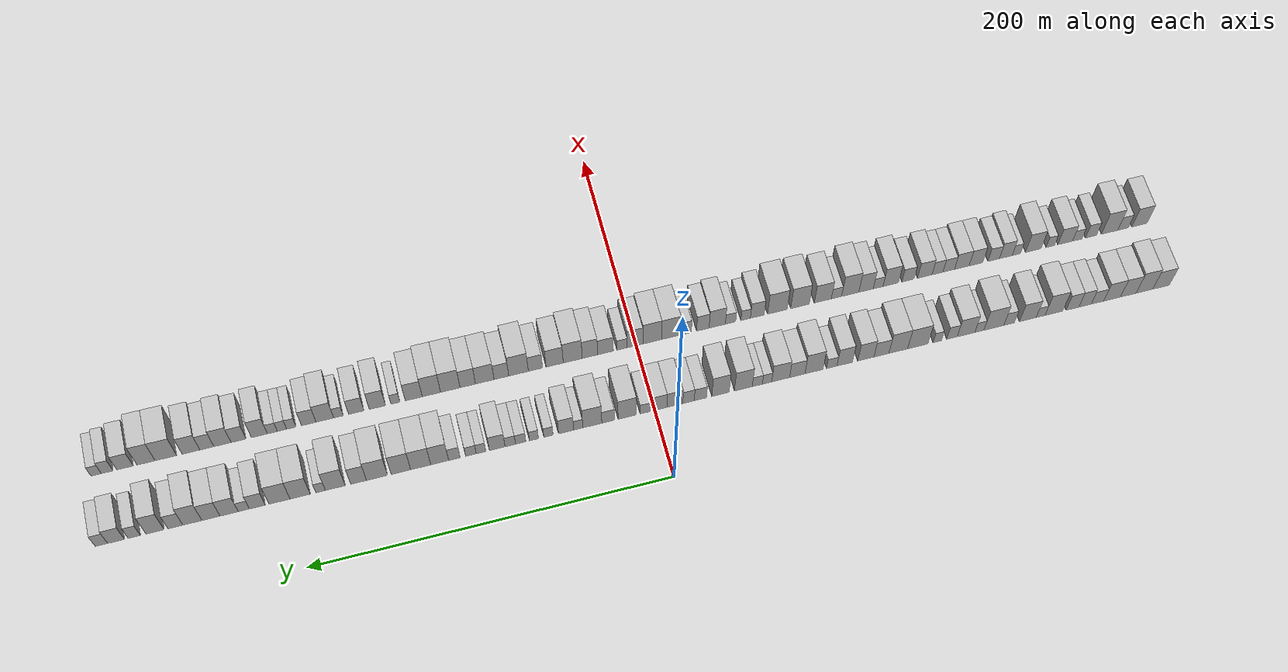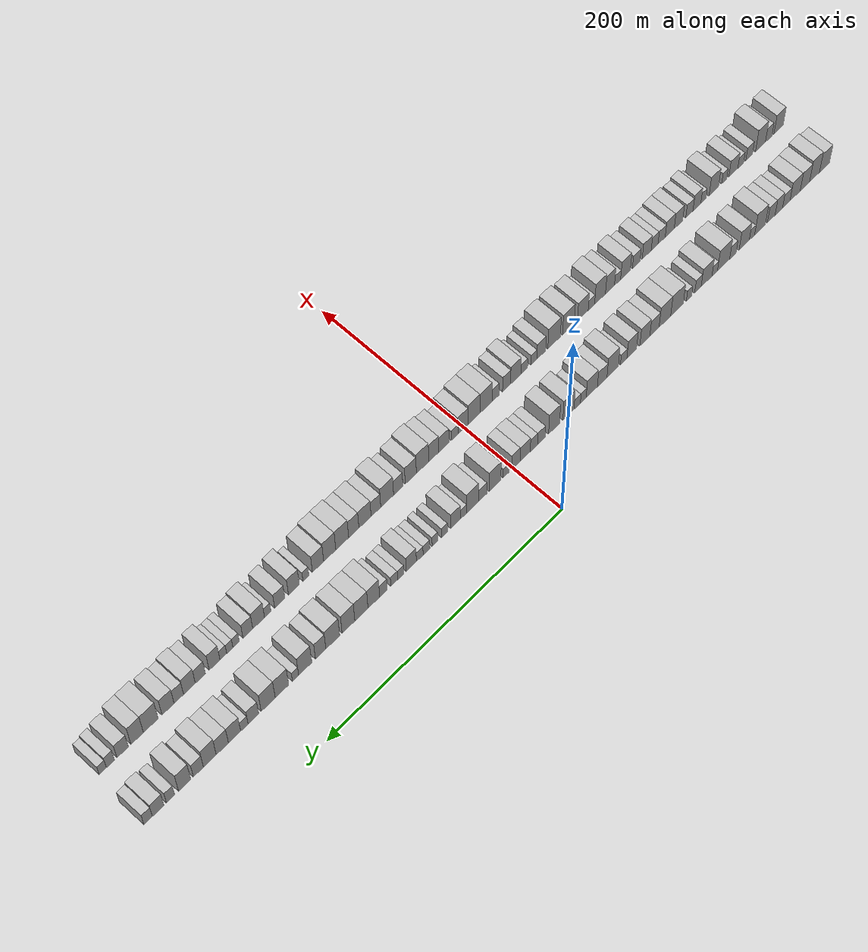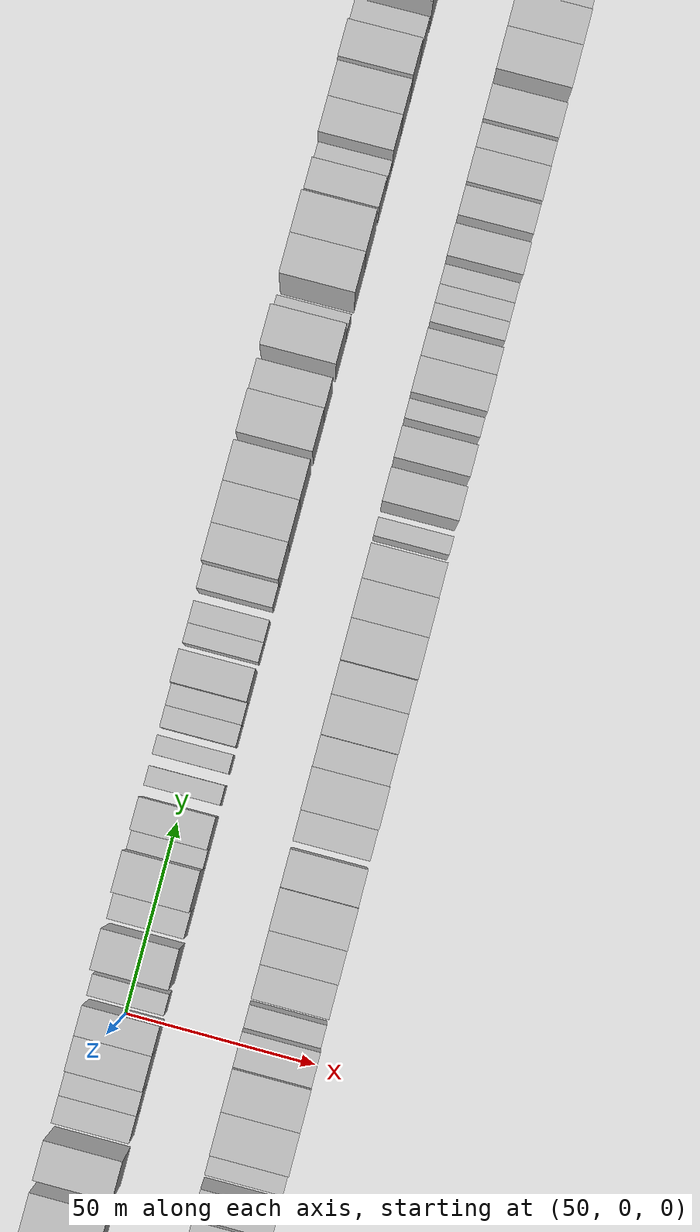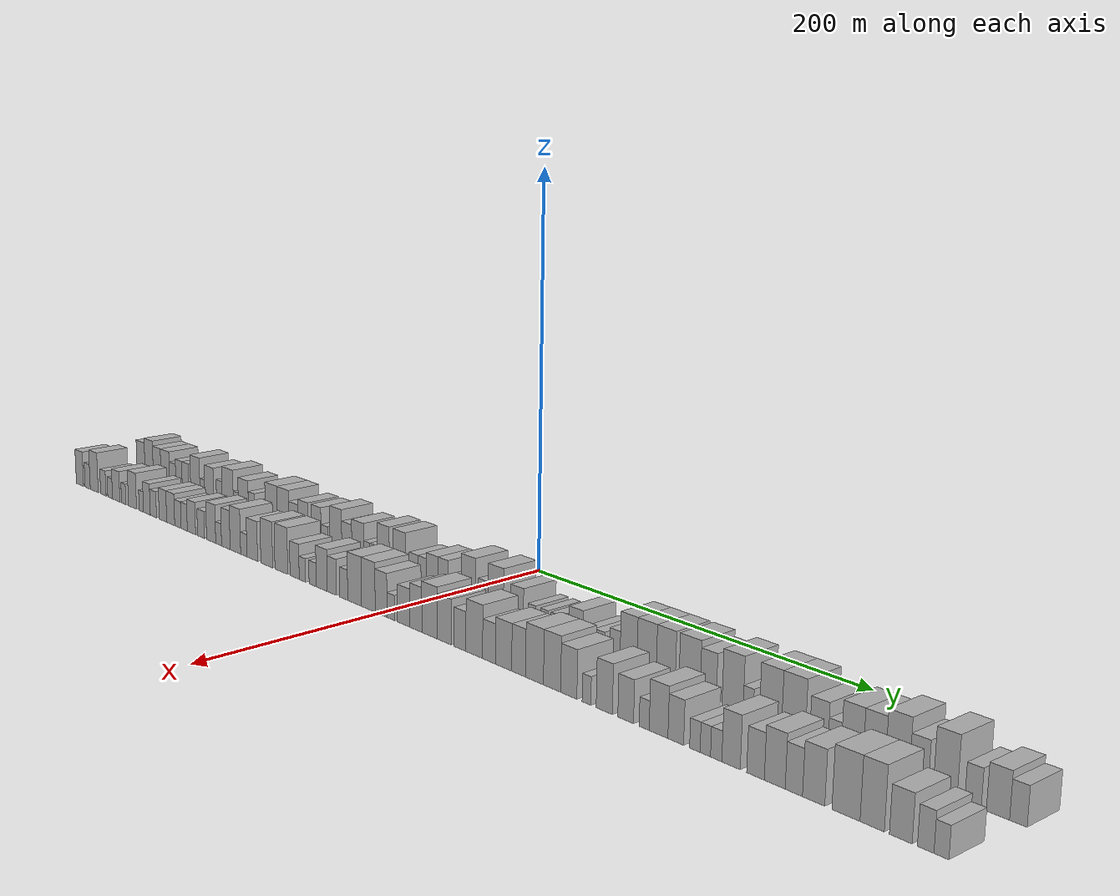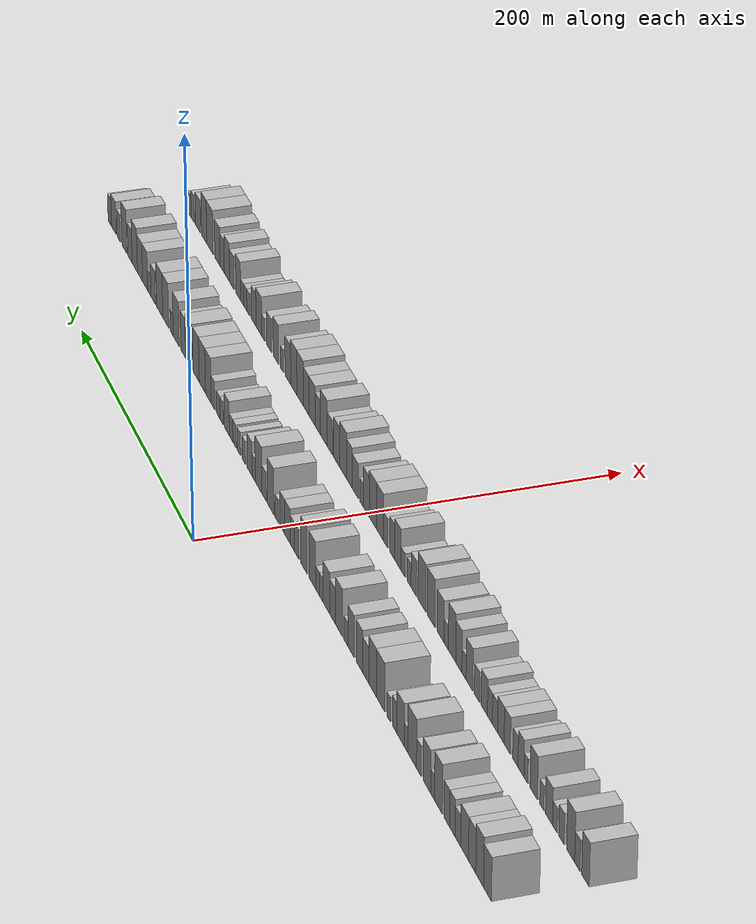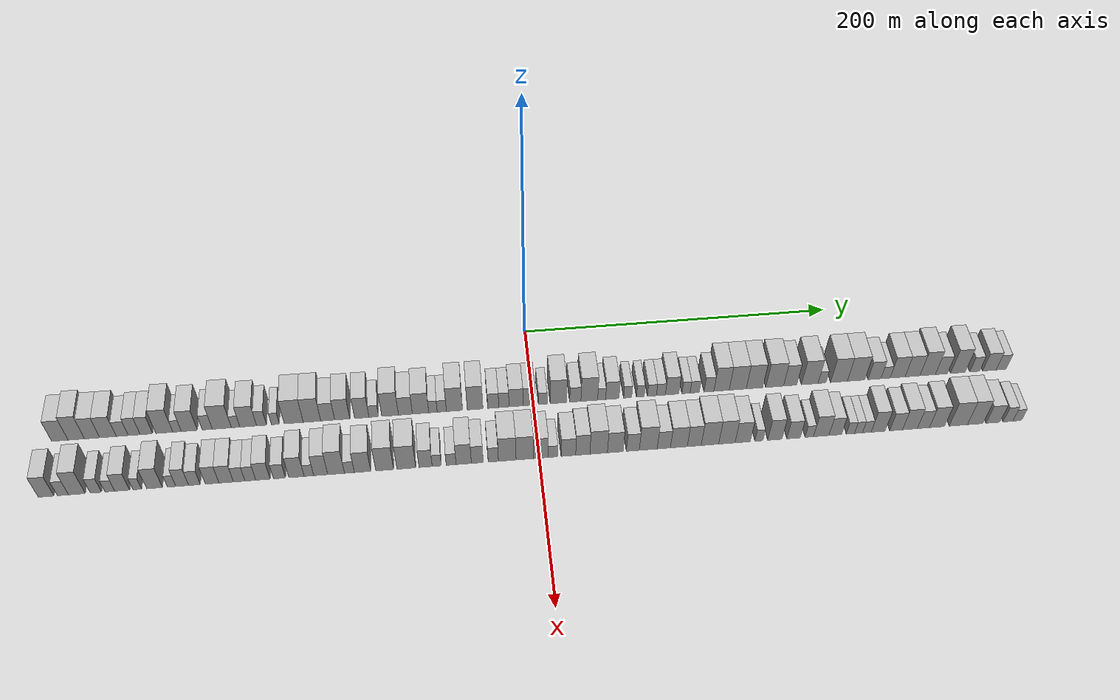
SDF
<sdf version="1.6">
 <world name="default">
  <scene>
   <sky><clouds><speed>12</speed></clouds></sky>
   <ambient>0.4 0.4 0.4 1</ambient>
   <background>0.7 0.7 0.7 1</background>
   <shadows>1</shadows>
  </scene>
  <gravity>0 0 -9.8066</gravity>
  <magnetic_field>6e-06 2.3e-05 -4.2e-05</magnetic_field>
  <physics default="0" name="default_physics" type="ode">
   <ode>
    <solver>
     <type>quick</type>
     <iters>10</iters>
     <sor>1.0</sor>
     <use_dynamic_moi_rescaling>0</use_dynamic_moi_rescaling>
    </solver>
    <constraints>
     <cfm>0</cfm>
     <erp>0.2</erp>
     <contact_max_correcting_vel>100</contact_max_correcting_vel>
     <contact_surface_layer>0.001</contact_surface_layer>
    </constraints>
   </ode>
   <max_step_size>0.004</max_step_size>
   <real_time_factor>1</real_time_factor>
   <real_time_update_rate>250</real_time_update_rate>
  </physics>
  <light name="sun" type="directional">
   <pose>0 0 10 0 0 0</pose>
   <diffuse>0.8 0.8 0.8 1</diffuse>
   <specular>0.2 0.2 0.2 1</specular>
   <attenuation>
    <range>1000</range>
    <constant>0.9</constant>
    <linear>0.01</linear>
    <quadratic>0.001</quadratic>
   </attenuation>
   <direction>-0.5 0.1 -0.9</direction>
  </light>
  <model name="building_1">
   <static>1</static>
   <pose>50.0000 -293.0404 0 0.000000 0.000000 0.000000</pose>
   <link name="link">
    <pose>0 0 10.50 0 0 0</pose>
    <collision name="collision"><geometry><box><size>20.0000 9.9192 21.0000</size></box></geometry></collision>
    <visual name="visual">
     <cast_shadows>0</cast_shadows>
     <geometry><box><size>20.0000 9.9192 21.0000</size></box></geometry>
     <material>
      <script>
       <uri>model://HANNAS_wall/materials/scripts</uri>
       <uri>model://HANNAS_wall/materials/textures</uri>
       <name>vrc/HANNAS_wall</name>
      </script>
     </material>
    </visual>
   </link>
  </model>
  <model name="building_2">
   <static>1</static>
   <pose>50.0000 -283.0995 0 0.000000 0.000000 0.000000</pose>
   <link name="link">
    <pose>0 0 12.00 0 0 0</pose>
    <collision name="collision"><geometry><box><size>20.0000 9.9627 24.0000</size></box></geometry></collision>
    <visual name="visual">
     <cast_shadows>0</cast_shadows>
     <geometry><box><size>20.0000 9.9627 24.0000</size></box></geometry>
     <material>
      <script>
       <uri>model://HANNAS_wall/materials/scripts</uri>
       <uri>model://HANNAS_wall/materials/textures</uri>
       <name>vrc/HANNAS_wall</name>
      </script>
     </material>
    </visual>
   </link>
  </model>
  <model name="building_3">
   <static>1</static>
   <pose>50.0000 -273.4754 0 0.000000 0.000000 0.000000</pose>
   <link name="link">
    <pose>0 0 10.50 0 0 0</pose>
    <collision name="collision"><geometry><box><size>20.0000 9.2853 21.0000</size></box></geometry></collision>
    <visual name="visual">
     <cast_shadows>0</cast_shadows>
     <geometry><box><size>20.0000 9.2853 21.0000</size></box></geometry>
     <material>
      <script>
       <uri>model://HANNAS_wall/materials/scripts</uri>
       <uri>model://HANNAS_wall/materials/textures</uri>
       <name>vrc/HANNAS_wall</name>
      </script>
     </material>
    </visual>
   </link>
  </model>
  <model name="building_4">
   <static>1</static>
   <pose>50.0000 -263.8147 0 0.000000 0.000000 0.000000</pose>
   <link name="link">
    <pose>0 0 10.50 0 0 0</pose>
    <collision name="collision"><geometry><box><size>20.0000 10.0361 21.0000</size></box></geometry></collision>
    <visual name="visual">
     <cast_shadows>0</cast_shadows>
     <geometry><box><size>20.0000 10.0361 21.0000</size></box></geometry>
     <material>
      <script>
       <uri>model://HANNAS_wall/materials/scripts</uri>
       <uri>model://HANNAS_wall/materials/textures</uri>
       <name>vrc/HANNAS_wall</name>
      </script>
     </material>
    </visual>
   </link>
  </model>
  <model name="building_5">
   <static>1</static>
   <pose>50.0000 -255.1313 0 0.000000 0.000000 0.000000</pose>
   <link name="link">
    <pose>0 0 7.50 0 0 0</pose>
    <collision name="collision"><geometry><box><size>20.0000 7.3308 15.0000</size></box></geometry></collision>
    <visual name="visual">
     <cast_shadows>0</cast_shadows>
     <geometry><box><size>20.0000 7.3308 15.0000</size></box></geometry>
     <material>
      <script>
       <uri>model://HANNAS_wall/materials/scripts</uri>
       <uri>model://HANNAS_wall/materials/textures</uri>
       <name>vrc/HANNAS_wall</name>
      </script>
     </material>
    </visual>
   </link>
  </model>
  <model name="building_6">
   <static>1</static>
   <pose>50.0000 -247.8303 0 0.000000 0.000000 0.000000</pose>
   <link name="link">
    <pose>0 0 9.00 0 0 0</pose>
    <collision name="collision"><geometry><box><size>20.0000 7.2713 18.0000</size></box></geometry></collision>
    <visual name="visual">
     <cast_shadows>0</cast_shadows>
     <geometry><box><size>20.0000 7.2713 18.0000</size></box></geometry>
     <material>
      <script>
       <uri>model://HANNAS_wall/materials/scripts</uri>
       <uri>model://HANNAS_wall/materials/textures</uri>
       <name>vrc/HANNAS_wall</name>
      </script>
     </material>
    </visual>
   </link>
  </model>
  <model name="building_7">
   <static>1</static>
   <pose>50.0000 -240.4107 0 0.000000 0.000000 0.000000</pose>
   <link name="link">
    <pose>0 0 9.00 0 0 0</pose>
    <collision name="collision"><geometry><box><size>20.0000 7.5679 18.0000</size></box></geometry></collision>
    <visual name="visual">
     <cast_shadows>0</cast_shadows>
     <geometry><box><size>20.0000 7.5679 18.0000</size></box></geometry>
     <material>
      <script>
       <uri>model://HANNAS_wall/materials/scripts</uri>
       <uri>model://HANNAS_wall/materials/textures</uri>
       <name>vrc/HANNAS_wall</name>
      </script>
     </material>
    </visual>
   </link>
  </model>
  <model name="building_8">
   <static>1</static>
   <pose>50.0000 -229.4162 0 0.000000 0.000000 0.000000</pose>
   <link name="link">
    <pose>0 0 12.00 0 0 0</pose>
    <collision name="collision"><geometry><box><size>20.0000 10.4211 24.0000</size></box></geometry></collision>
    <visual name="visual">
     <cast_shadows>0</cast_shadows>
     <geometry><box><size>20.0000 10.4211 24.0000</size></box></geometry>
     <material>
      <script>
       <uri>model://HANNAS_wall/materials/scripts</uri>
       <uri>model://HANNAS_wall/materials/textures</uri>
       <name>vrc/HANNAS_wall</name>
      </script>
     </material>
    </visual>
   </link>
  </model>
  <model name="building_9">
   <static>1</static>
   <pose>50.0000 -221.6135 0 0.000000 0.000000 0.000000</pose>
   <link name="link">
    <pose>0 0 6.00 0 0 0</pose>
    <collision name="collision"><geometry><box><size>20.0000 5.1843 12.0000</size></box></geometry></collision>
    <visual name="visual">
     <cast_shadows>0</cast_shadows>
     <geometry><box><size>20.0000 5.1843 12.0000</size></box></geometry>
     <material>
      <script>
       <uri>model://HANNAS_wall/materials/scripts</uri>
       <uri>model://HANNAS_wall/materials/textures</uri>
       <name>vrc/HANNAS_wall</name>
      </script>
     </material>
    </visual>
   </link>
  </model>
  <model name="building_10">
   <static>1</static>
   <pose>50.0000 -214.1070 0 0.000000 0.000000 0.000000</pose>
   <link name="link">
    <pose>0 0 10.50 0 0 0</pose>
    <collision name="collision"><geometry><box><size>20.0000 9.8287 21.0000</size></box></geometry></collision>
    <visual name="visual">
     <cast_shadows>0</cast_shadows>
     <geometry><box><size>20.0000 9.8287 21.0000</size></box></geometry>
     <material>
      <script>
       <uri>model://HANNAS_wall/materials/scripts</uri>
       <uri>model://HANNAS_wall/materials/textures</uri>
       <name>vrc/HANNAS_wall</name>
      </script>
     </material>
    </visual>
   </link>
  </model>
  <model name="building_11">
   <static>1</static>
   <pose>50.0000 -203.1111 0 0.000000 0.000000 0.000000</pose>
   <link name="link">
    <pose>0 0 7.50 0 0 0</pose>
    <collision name="collision"><geometry><box><size>20.0000 6.1631 15.0000</size></box></geometry></collision>
    <visual name="visual">
     <cast_shadows>0</cast_shadows>
     <geometry><box><size>20.0000 6.1631 15.0000</size></box></geometry>
     <material>
      <script>
       <uri>model://HANNAS_wall/materials/scripts</uri>
       <uri>model://HANNAS_wall/materials/textures</uri>
       <name>vrc/HANNAS_wall</name>
      </script>
     </material>
    </visual>
   </link>
  </model>
  <model name="building_12">
   <static>1</static>
   <pose>50.0000 -194.1699 0 0.000000 0.000000 0.000000</pose>
   <link name="link">
    <pose>0 0 12.00 0 0 0</pose>
    <collision name="collision"><geometry><box><size>20.0000 11.7193 24.0000</size></box></geometry></collision>
    <visual name="visual">
     <cast_shadows>0</cast_shadows>
     <geometry><box><size>20.0000 11.7193 24.0000</size></box></geometry>
     <material>
      <script>
       <uri>model://HANNAS_wall/materials/scripts</uri>
       <uri>model://HANNAS_wall/materials/textures</uri>
       <name>vrc/HANNAS_wall</name>
      </script>
     </material>
    </visual>
   </link>
  </model>
  <model name="building_13">
   <static>1</static>
   <pose>50.0000 -185.6866 0 0.000000 0.000000 0.000000</pose>
   <link name="link">
    <pose>0 0 6.00 0 0 0</pose>
    <collision name="collision"><geometry><box><size>20.0000 5.2473 12.0000</size></box></geometry></collision>
    <visual name="visual">
     <cast_shadows>0</cast_shadows>
     <geometry><box><size>20.0000 5.2473 12.0000</size></box></geometry>
     <material>
      <script>
       <uri>model://HANNAS_wall/materials/scripts</uri>
       <uri>model://HANNAS_wall/materials/textures</uri>
       <name>vrc/HANNAS_wall</name>
      </script>
     </material>
    </visual>
   </link>
  </model>
  <model name="building_14">
   <static>1</static>
   <pose>50.0000 -177.9145 0 0.000000 0.000000 0.000000</pose>
   <link name="link">
    <pose>0 0 10.50 0 0 0</pose>
    <collision name="collision"><geometry><box><size>20.0000 10.2970 21.0000</size></box></geometry></collision>
    <visual name="visual">
     <cast_shadows>0</cast_shadows>
     <geometry><box><size>20.0000 10.2970 21.0000</size></box></geometry>
     <material>
      <script>
       <uri>model://HANNAS_wall/materials/scripts</uri>
       <uri>model://HANNAS_wall/materials/textures</uri>
       <name>vrc/HANNAS_wall</name>
      </script>
     </material>
    </visual>
   </link>
  </model>
  <model name="building_15">
   <static>1</static>
   <pose>50.0000 -169.6922 0 0.000000 0.000000 0.000000</pose>
   <link name="link">
    <pose>0 0 7.50 0 0 0</pose>
    <collision name="collision"><geometry><box><size>20.0000 6.1476 15.0000</size></box></geometry></collision>
    <visual name="visual">
     <cast_shadows>0</cast_shadows>
     <geometry><box><size>20.0000 6.1476 15.0000</size></box></geometry>
     <material>
      <script>
       <uri>model://HANNAS_wall/materials/scripts</uri>
       <uri>model://HANNAS_wall/materials/textures</uri>
       <name>vrc/HANNAS_wall</name>
      </script>
     </material>
    </visual>
   </link>
  </model>
  <model name="building_16">
   <static>1</static>
   <pose>50.0000 -161.1644 0 0.000000 0.000000 0.000000</pose>
   <link name="link">
    <pose>0 0 6.00 0 0 0</pose>
    <collision name="collision"><geometry><box><size>20.0000 4.9079 12.0000</size></box></geometry></collision>
    <visual name="visual">
     <cast_shadows>0</cast_shadows>
     <geometry><box><size>20.0000 4.9079 12.0000</size></box></geometry>
     <material>
      <script>
       <uri>model://HANNAS_wall/materials/scripts</uri>
       <uri>model://HANNAS_wall/materials/textures</uri>
       <name>vrc/HANNAS_wall</name>
      </script>
     </material>
    </visual>
   </link>
  </model>
  <model name="building_17">
   <static>1</static>
   <pose>50.0000 -149.8009 0 0.000000 0.000000 0.000000</pose>
   <link name="link">
    <pose>0 0 12.00 0 0 0</pose>
    <collision name="collision"><geometry><box><size>20.0000 11.8191 24.0000</size></box></geometry></collision>
    <visual name="visual">
     <cast_shadows>0</cast_shadows>
     <geometry><box><size>20.0000 11.8191 24.0000</size></box></geometry>
     <material>
      <script>
       <uri>model://HANNAS_wall/materials/scripts</uri>
       <uri>model://HANNAS_wall/materials/textures</uri>
       <name>vrc/HANNAS_wall</name>
      </script>
     </material>
    </visual>
   </link>
  </model>
  <model name="building_18">
   <static>1</static>
   <pose>50.0000 -138.4631 0 0.000000 0.000000 0.000000</pose>
   <link name="link">
    <pose>0 0 12.00 0 0 0</pose>
    <collision name="collision"><geometry><box><size>20.0000 10.8565 24.0000</size></box></geometry></collision>
    <visual name="visual">
     <cast_shadows>0</cast_shadows>
     <geometry><box><size>20.0000 10.8565 24.0000</size></box></geometry>
     <material>
      <script>
       <uri>model://HANNAS_wall/materials/scripts</uri>
       <uri>model://HANNAS_wall/materials/textures</uri>
       <name>vrc/HANNAS_wall</name>
      </script>
     </material>
    </visual>
   </link>
  </model>
  <model name="building_19">
   <static>1</static>
   <pose>50.0000 -128.7146 0 0.000000 0.000000 0.000000</pose>
   <link name="link">
    <pose>0 0 9.00 0 0 0</pose>
    <collision name="collision"><geometry><box><size>20.0000 8.6404 18.0000</size></box></geometry></collision>
    <visual name="visual">
     <cast_shadows>0</cast_shadows>
     <geometry><box><size>20.0000 8.6404 18.0000</size></box></geometry>
     <material>
      <script>
       <uri>model://HANNAS_wall/materials/scripts</uri>
       <uri>model://HANNAS_wall/materials/textures</uri>
       <name>vrc/HANNAS_wall</name>
      </script>
     </material>
    </visual>
   </link>
  </model>
  <model name="building_20">
   <static>1</static>
   <pose>50.0000 -119.7162 0 0.000000 0.000000 0.000000</pose>
   <link name="link">
    <pose>0 0 10.50 0 0 0</pose>
    <collision name="collision"><geometry><box><size>20.0000 9.3563 21.0000</size></box></geometry></collision>
    <visual name="visual">
     <cast_shadows>0</cast_shadows>
     <geometry><box><size>20.0000 9.3563 21.0000</size></box></geometry>
     <material>
      <script>
       <uri>model://HANNAS_wall/materials/scripts</uri>
       <uri>model://HANNAS_wall/materials/textures</uri>
       <name>vrc/HANNAS_wall</name>
      </script>
     </material>
    </visual>
   </link>
  </model>
  <model name="building_21">
   <static>1</static>
   <pose>50.0000 -107.5606 0 0.000000 0.000000 0.000000</pose>
   <link name="link">
    <pose>0 0 10.50 0 0 0</pose>
    <collision name="collision"><geometry><box><size>20.0000 8.9550 21.0000</size></box></geometry></collision>
    <visual name="visual">
     <cast_shadows>0</cast_shadows>
     <geometry><box><size>20.0000 8.9550 21.0000</size></box></geometry>
     <material>
      <script>
       <uri>model://HANNAS_wall/materials/scripts</uri>
       <uri>model://HANNAS_wall/materials/textures</uri>
       <name>vrc/HANNAS_wall</name>
      </script>
     </material>
    </visual>
   </link>
  </model>
  <model name="building_22">
   <static>1</static>
   <pose>50.0000 -100.0929 0 0.000000 0.000000 0.000000</pose>
   <link name="link">
    <pose>0 0 6.00 0 0 0</pose>
    <collision name="collision"><geometry><box><size>20.0000 5.9805 12.0000</size></box></geometry></collision>
    <visual name="visual">
     <cast_shadows>0</cast_shadows>
     <geometry><box><size>20.0000 5.9805 12.0000</size></box></geometry>
     <material>
      <script>
       <uri>model://HANNAS_wall/materials/scripts</uri>
       <uri>model://HANNAS_wall/materials/textures</uri>
       <name>vrc/HANNAS_wall</name>
      </script>
     </material>
    </visual>
   </link>
  </model>
  <model name="building_23">
   <static>1</static>
   <pose>50.0000 -89.9068 0 0.000000 0.000000 0.000000</pose>
   <link name="link">
    <pose>0 0 12.00 0 0 0</pose>
    <collision name="collision"><geometry><box><size>20.0000 10.3917 24.0000</size></box></geometry></collision>
    <visual name="visual">
     <cast_shadows>0</cast_shadows>
     <geometry><box><size>20.0000 10.3917 24.0000</size></box></geometry>
     <material>
      <script>
       <uri>model://HANNAS_wall/materials/scripts</uri>
       <uri>model://HANNAS_wall/materials/textures</uri>
       <name>vrc/HANNAS_wall</name>
      </script>
     </material>
    </visual>
   </link>
  </model>
  <model name="building_24">
   <static>1</static>
   <pose>50.0000 -80.3440 0 0.000000 0.000000 0.000000</pose>
   <link name="link">
    <pose>0 0 9.00 0 0 0</pose>
    <collision name="collision"><geometry><box><size>20.0000 8.7340 18.0000</size></box></geometry></collision>
    <visual name="visual">
     <cast_shadows>0</cast_shadows>
     <geometry><box><size>20.0000 8.7340 18.0000</size></box></geometry>
     <material>
      <script>
       <uri>model://HANNAS_wall/materials/scripts</uri>
       <uri>model://HANNAS_wall/materials/textures</uri>
       <name>vrc/HANNAS_wall</name>
      </script>
     </material>
    </visual>
   </link>
  </model>
  <model name="building_25">
   <static>1</static>
   <pose>50.0000 -70.8512 0 0.000000 0.000000 0.000000</pose>
   <link name="link">
    <pose>0 0 10.50 0 0 0</pose>
    <collision name="collision"><geometry><box><size>20.0000 10.2515 21.0000</size></box></geometry></collision>
    <visual name="visual">
     <cast_shadows>0</cast_shadows>
     <geometry><box><size>20.0000 10.2515 21.0000</size></box></geometry>
     <material>
      <script>
       <uri>model://HANNAS_wall/materials/scripts</uri>
       <uri>model://HANNAS_wall/materials/textures</uri>
       <name>vrc/HANNAS_wall</name>
      </script>
     </material>
    </visual>
   </link>
  </model>
  <model name="building_26">
   <static>1</static>
   <pose>50.0000 -63.0987 0 0.000000 0.000000 0.000000</pose>
   <link name="link">
    <pose>0 0 6.00 0 0 0</pose>
    <collision name="collision"><geometry><box><size>20.0000 5.2537 12.0000</size></box></geometry></collision>
    <visual name="visual">
     <cast_shadows>0</cast_shadows>
     <geometry><box><size>20.0000 5.2537 12.0000</size></box></geometry>
     <material>
      <script>
       <uri>model://HANNAS_wall/materials/scripts</uri>
       <uri>model://HANNAS_wall/materials/textures</uri>
       <name>vrc/HANNAS_wall</name>
      </script>
     </material>
    </visual>
   </link>
  </model>
  <model name="building_27">
   <static>1</static>
   <pose>50.0000 -57.5809 0 0.000000 0.000000 0.000000</pose>
   <link name="link">
    <pose>0 0 6.00 0 0 0</pose>
    <collision name="collision"><geometry><box><size>20.0000 5.7818 12.0000</size></box></geometry></collision>
    <visual name="visual">
     <cast_shadows>0</cast_shadows>
     <geometry><box><size>20.0000 5.7818 12.0000</size></box></geometry>
     <material>
      <script>
       <uri>model://HANNAS_wall/materials/scripts</uri>
       <uri>model://HANNAS_wall/materials/textures</uri>
       <name>vrc/HANNAS_wall</name>
      </script>
     </material>
    </visual>
   </link>
  </model>
  <model name="building_28">
   <static>1</static>
   <pose>50.0000 -49.6364 0 0.000000 0.000000 0.000000</pose>
   <link name="link">
    <pose>0 0 12.00 0 0 0</pose>
    <collision name="collision"><geometry><box><size>20.0000 10.1071 24.0000</size></box></geometry></collision>
    <visual name="visual">
     <cast_shadows>0</cast_shadows>
     <geometry><box><size>20.0000 10.1071 24.0000</size></box></geometry>
     <material>
      <script>
       <uri>model://HANNAS_wall/materials/scripts</uri>
       <uri>model://HANNAS_wall/materials/textures</uri>
       <name>vrc/HANNAS_wall</name>
      </script>
     </material>
    </visual>
   </link>
  </model>
  <model name="building_29">
   <static>1</static>
   <pose>50.0000 -36.6501 0 0.000000 0.000000 0.000000</pose>
   <link name="link">
    <pose>0 0 12.00 0 0 0</pose>
    <collision name="collision"><geometry><box><size>20.0000 9.8655 24.0000</size></box></geometry></collision>
    <visual name="visual">
     <cast_shadows>0</cast_shadows>
     <geometry><box><size>20.0000 9.8655 24.0000</size></box></geometry>
     <material>
      <script>
       <uri>model://HANNAS_wall/materials/scripts</uri>
       <uri>model://HANNAS_wall/materials/textures</uri>
       <name>vrc/HANNAS_wall</name>
      </script>
     </material>
    </visual>
   </link>
  </model>
  <model name="building_30">
   <static>1</static>
   <pose>50.0000 -25.2569 0 0.000000 0.000000 0.000000</pose>
   <link name="link">
    <pose>0 0 7.50 0 0 0</pose>
    <collision name="collision"><geometry><box><size>20.0000 6.9210 15.0000</size></box></geometry></collision>
    <visual name="visual">
     <cast_shadows>0</cast_shadows>
     <geometry><box><size>20.0000 6.9210 15.0000</size></box></geometry>
     <material>
      <script>
       <uri>model://HANNAS_wall/materials/scripts</uri>
       <uri>model://HANNAS_wall/materials/textures</uri>
       <name>vrc/HANNAS_wall</name>
      </script>
     </material>
    </visual>
   </link>
  </model>
  <model name="building_31">
   <static>1</static>
   <pose>50.0000 -18.5693 0 0.000000 0.000000 0.000000</pose>
   <link name="link">
    <pose>0 0 7.50 0 0 0</pose>
    <collision name="collision"><geometry><box><size>20.0000 6.4541 15.0000</size></box></geometry></collision>
    <visual name="visual">
     <cast_shadows>0</cast_shadows>
     <geometry><box><size>20.0000 6.4541 15.0000</size></box></geometry>
     <material>
      <script>
       <uri>model://HANNAS_wall/materials/scripts</uri>
       <uri>model://HANNAS_wall/materials/textures</uri>
       <name>vrc/HANNAS_wall</name>
      </script>
     </material>
    </visual>
   </link>
  </model>
  <model name="building_32">
   <static>1</static>
   <pose>50.0000 -10.8621 0 0.000000 0.000000 0.000000</pose>
   <link name="link">
    <pose>0 0 9.00 0 0 0</pose>
    <collision name="collision"><geometry><box><size>20.0000 8.9603 18.0000</size></box></geometry></collision>
    <visual name="visual">
     <cast_shadows>0</cast_shadows>
     <geometry><box><size>20.0000 8.9603 18.0000</size></box></geometry>
     <material>
      <script>
       <uri>model://HANNAS_wall/materials/scripts</uri>
       <uri>model://HANNAS_wall/materials/textures</uri>
       <name>vrc/HANNAS_wall</name>
      </script>
     </material>
    </visual>
   </link>
  </model>
  <model name="building_33">
   <static>1</static>
   <pose>50.0000 -2.5638 0 0.000000 0.000000 0.000000</pose>
   <link name="link">
    <pose>0 0 9.00 0 0 0</pose>
    <collision name="collision"><geometry><box><size>20.0000 7.6363 18.0000</size></box></geometry></collision>
    <visual name="visual">
     <cast_shadows>0</cast_shadows>
     <geometry><box><size>20.0000 7.6363 18.0000</size></box></geometry>
     <material>
      <script>
       <uri>model://HANNAS_wall/materials/scripts</uri>
       <uri>model://HANNAS_wall/materials/textures</uri>
       <name>vrc/HANNAS_wall</name>
      </script>
     </material>
    </visual>
   </link>
  </model>
  <model name="building_34">
   <static>1</static>
   <pose>50.0000 5.9958 0 0.000000 0.000000 0.000000</pose>
   <link name="link">
    <pose>0 0 6.00 0 0 0</pose>
    <collision name="collision"><geometry><box><size>20.0000 5.4830 12.0000</size></box></geometry></collision>
    <visual name="visual">
     <cast_shadows>0</cast_shadows>
     <geometry><box><size>20.0000 5.4830 12.0000</size></box></geometry>
     <material>
      <script>
       <uri>model://HANNAS_wall/materials/scripts</uri>
       <uri>model://HANNAS_wall/materials/textures</uri>
       <name>vrc/HANNAS_wall</name>
      </script>
     </material>
    </visual>
   </link>
  </model>
  <model name="building_35">
   <static>1</static>
   <pose>50.0000 15.9093 0 0.000000 0.000000 0.000000</pose>
   <link name="link">
    <pose>0 0 12.00 0 0 0</pose>
    <collision name="collision"><geometry><box><size>20.0000 10.3439 24.0000</size></box></geometry></collision>
    <visual name="visual">
     <cast_shadows>0</cast_shadows>
     <geometry><box><size>20.0000 10.3439 24.0000</size></box></geometry>
     <material>
      <script>
       <uri>model://HANNAS_wall/materials/scripts</uri>
       <uri>model://HANNAS_wall/materials/textures</uri>
       <name>vrc/HANNAS_wall</name>
      </script>
     </material>
    </visual>
   </link>
  </model>
  <model name="building_36">
   <static>1</static>
   <pose>50.0000 26.6475 0 0.000000 0.000000 0.000000</pose>
   <link name="link">
    <pose>0 0 7.50 0 0 0</pose>
    <collision name="collision"><geometry><box><size>20.0000 7.1325 15.0000</size></box></geometry></collision>
    <visual name="visual">
     <cast_shadows>0</cast_shadows>
     <geometry><box><size>20.0000 7.1325 15.0000</size></box></geometry>
     <material>
      <script>
       <uri>model://HANNAS_wall/materials/scripts</uri>
       <uri>model://HANNAS_wall/materials/textures</uri>
       <name>vrc/HANNAS_wall</name>
      </script>
     </material>
    </visual>
   </link>
  </model>
  <model name="building_37">
   <static>1</static>
   <pose>50.0000 35.5171 0 0.000000 0.000000 0.000000</pose>
   <link name="link">
    <pose>0 0 12.00 0 0 0</pose>
    <collision name="collision"><geometry><box><size>20.0000 10.6068 24.0000</size></box></geometry></collision>
    <visual name="visual">
     <cast_shadows>0</cast_shadows>
     <geometry><box><size>20.0000 10.6068 24.0000</size></box></geometry>
     <material>
      <script>
       <uri>model://HANNAS_wall/materials/scripts</uri>
       <uri>model://HANNAS_wall/materials/textures</uri>
       <name>vrc/HANNAS_wall</name>
      </script>
     </material>
    </visual>
   </link>
  </model>
  <model name="building_38">
   <static>1</static>
   <pose>50.0000 43.3631 0 0.000000 0.000000 0.000000</pose>
   <link name="link">
    <pose>0 0 6.00 0 0 0</pose>
    <collision name="collision"><geometry><box><size>20.0000 5.0853 12.0000</size></box></geometry></collision>
    <visual name="visual">
     <cast_shadows>0</cast_shadows>
     <geometry><box><size>20.0000 5.0853 12.0000</size></box></geometry>
     <material>
      <script>
       <uri>model://HANNAS_wall/materials/scripts</uri>
       <uri>model://HANNAS_wall/materials/textures</uri>
       <name>vrc/HANNAS_wall</name>
      </script>
     </material>
    </visual>
   </link>
  </model>
  <model name="building_39">
   <static>1</static>
   <pose>50.0000 50.1533 0 0.000000 0.000000 0.000000</pose>
   <link name="link">
    <pose>0 0 9.00 0 0 0</pose>
    <collision name="collision"><geometry><box><size>20.0000 8.4950 18.0000</size></box></geometry></collision>
    <visual name="visual">
     <cast_shadows>0</cast_shadows>
     <geometry><box><size>20.0000 8.4950 18.0000</size></box></geometry>
     <material>
      <script>
       <uri>model://HANNAS_wall/materials/scripts</uri>
       <uri>model://HANNAS_wall/materials/textures</uri>
       <name>vrc/HANNAS_wall</name>
      </script>
     </material>
    </visual>
   </link>
  </model>
  <model name="building_40">
   <static>1</static>
   <pose>50.0000 59.9617 0 0.000000 0.000000 0.000000</pose>
   <link name="link">
    <pose>0 0 6.00 0 0 0</pose>
    <collision name="collision"><geometry><box><size>20.0000 5.1219 12.0000</size></box></geometry></collision>
    <visual name="visual">
     <cast_shadows>0</cast_shadows>
     <geometry><box><size>20.0000 5.1219 12.0000</size></box></geometry>
     <material>
      <script>
       <uri>model://HANNAS_wall/materials/scripts</uri>
       <uri>model://HANNAS_wall/materials/textures</uri>
       <name>vrc/HANNAS_wall</name>
      </script>
     </material>
    </visual>
   </link>
  </model>
  <model name="building_41">
   <static>1</static>
   <pose>50.0000 68.0322 0 0.000000 0.000000 0.000000</pose>
   <link name="link">
    <pose>0 0 6.00 0 0 0</pose>
    <collision name="collision"><geometry><box><size>20.0000 5.0191 12.0000</size></box></geometry></collision>
    <visual name="visual">
     <cast_shadows>0</cast_shadows>
     <geometry><box><size>20.0000 5.0191 12.0000</size></box></geometry>
     <material>
      <script>
       <uri>model://HANNAS_wall/materials/scripts</uri>
       <uri>model://HANNAS_wall/materials/textures</uri>
       <name>vrc/HANNAS_wall</name>
      </script>
     </material>
    </visual>
   </link>
  </model>
  <model name="building_42">
   <static>1</static>
   <pose>50.0000 75.4131 0 0.000000 0.000000 0.000000</pose>
   <link name="link">
    <pose>0 0 6.00 0 0 0</pose>
    <collision name="collision"><geometry><box><size>20.0000 5.7426 12.0000</size></box></geometry></collision>
    <visual name="visual">
     <cast_shadows>0</cast_shadows>
     <geometry><box><size>20.0000 5.7426 12.0000</size></box></geometry>
     <material>
      <script>
       <uri>model://HANNAS_wall/materials/scripts</uri>
       <uri>model://HANNAS_wall/materials/textures</uri>
       <name>vrc/HANNAS_wall</name>
      </script>
     </material>
    </visual>
   </link>
  </model>
  <model name="building_43">
   <static>1</static>
   <pose>50.0000 81.1697 0 0.000000 0.000000 0.000000</pose>
   <link name="link">
    <pose>0 0 6.00 0 0 0</pose>
    <collision name="collision"><geometry><box><size>20.0000 5.7707 12.0000</size></box></geometry></collision>
    <visual name="visual">
     <cast_shadows>0</cast_shadows>
     <geometry><box><size>20.0000 5.7707 12.0000</size></box></geometry>
     <material>
      <script>
       <uri>model://HANNAS_wall/materials/scripts</uri>
       <uri>model://HANNAS_wall/materials/textures</uri>
       <name>vrc/HANNAS_wall</name>
      </script>
     </material>
    </visual>
   </link>
  </model>
  <model name="building_44">
   <static>1</static>
   <pose>50.0000 88.3704 0 0.000000 0.000000 0.000000</pose>
   <link name="link">
    <pose>0 0 9.00 0 0 0</pose>
    <collision name="collision"><geometry><box><size>20.0000 8.6306 18.0000</size></box></geometry></collision>
    <visual name="visual">
     <cast_shadows>0</cast_shadows>
     <geometry><box><size>20.0000 8.6306 18.0000</size></box></geometry>
     <material>
      <script>
       <uri>model://HANNAS_wall/materials/scripts</uri>
       <uri>model://HANNAS_wall/materials/textures</uri>
       <name>vrc/HANNAS_wall</name>
      </script>
     </material>
    </visual>
   </link>
  </model>
  <model name="building_45">
   <static>1</static>
   <pose>50.0000 97.3139 0 0.000000 0.000000 0.000000</pose>
   <link name="link">
    <pose>0 0 6.00 0 0 0</pose>
    <collision name="collision"><geometry><box><size>20.0000 5.2565 12.0000</size></box></geometry></collision>
    <visual name="visual">
     <cast_shadows>0</cast_shadows>
     <geometry><box><size>20.0000 5.2565 12.0000</size></box></geometry>
     <material>
      <script>
       <uri>model://HANNAS_wall/materials/scripts</uri>
       <uri>model://HANNAS_wall/materials/textures</uri>
       <name>vrc/HANNAS_wall</name>
      </script>
     </material>
    </visual>
   </link>
  </model>
  <model name="building_46">
   <static>1</static>
   <pose>50.0000 102.8810 0 0.000000 0.000000 0.000000</pose>
   <link name="link">
    <pose>0 0 6.00 0 0 0</pose>
    <collision name="collision"><geometry><box><size>20.0000 5.8777 12.0000</size></box></geometry></collision>
    <visual name="visual">
     <cast_shadows>0</cast_shadows>
     <geometry><box><size>20.0000 5.8777 12.0000</size></box></geometry>
     <material>
      <script>
       <uri>model://HANNAS_wall/materials/scripts</uri>
       <uri>model://HANNAS_wall/materials/textures</uri>
       <name>vrc/HANNAS_wall</name>
      </script>
     </material>
    </visual>
   </link>
  </model>
  <model name="building_47">
   <static>1</static>
   <pose>50.0000 112.0094 0 0.000000 0.000000 0.000000</pose>
   <link name="link">
    <pose>0 0 7.50 0 0 0</pose>
    <collision name="collision"><geometry><box><size>20.0000 6.3789 15.0000</size></box></geometry></collision>
    <visual name="visual">
     <cast_shadows>0</cast_shadows>
     <geometry><box><size>20.0000 6.3789 15.0000</size></box></geometry>
     <material>
      <script>
       <uri>model://HANNAS_wall/materials/scripts</uri>
       <uri>model://HANNAS_wall/materials/textures</uri>
       <name>vrc/HANNAS_wall</name>
      </script>
     </material>
    </visual>
   </link>
  </model>
  <model name="building_48">
   <static>1</static>
   <pose>50.0000 120.1160 0 0.000000 0.000000 0.000000</pose>
   <link name="link">
    <pose>0 0 12.00 0 0 0</pose>
    <collision name="collision"><geometry><box><size>20.0000 9.8343 24.0000</size></box></geometry></collision>
    <visual name="visual">
     <cast_shadows>0</cast_shadows>
     <geometry><box><size>20.0000 9.8343 24.0000</size></box></geometry>
     <material>
      <script>
       <uri>model://HANNAS_wall/materials/scripts</uri>
       <uri>model://HANNAS_wall/materials/textures</uri>
       <name>vrc/HANNAS_wall</name>
      </script>
     </material>
    </visual>
   </link>
  </model>
  <model name="building_49">
   <static>1</static>
   <pose>50.0000 130.5367 0 0.000000 0.000000 0.000000</pose>
   <link name="link">
    <pose>0 0 12.00 0 0 0</pose>
    <collision name="collision"><geometry><box><size>20.0000 11.0071 24.0000</size></box></geometry></collision>
    <visual name="visual">
     <cast_shadows>0</cast_shadows>
     <geometry><box><size>20.0000 11.0071 24.0000</size></box></geometry>
     <material>
      <script>
       <uri>model://HANNAS_wall/materials/scripts</uri>
       <uri>model://HANNAS_wall/materials/textures</uri>
       <name>vrc/HANNAS_wall</name>
      </script>
     </material>
    </visual>
   </link>
  </model>
  <model name="building_50">
   <static>1</static>
   <pose>50.0000 141.3571 0 0.000000 0.000000 0.000000</pose>
   <link name="link">
    <pose>0 0 12.00 0 0 0</pose>
    <collision name="collision"><geometry><box><size>20.0000 10.6338 24.0000</size></box></geometry></collision>
    <visual name="visual">
     <cast_shadows>0</cast_shadows>
     <geometry><box><size>20.0000 10.6338 24.0000</size></box></geometry>
     <material>
      <script>
       <uri>model://HANNAS_wall/materials/scripts</uri>
       <uri>model://HANNAS_wall/materials/textures</uri>
       <name>vrc/HANNAS_wall</name>
      </script>
     </material>
    </visual>
   </link>
  </model>
  <model name="building_51">
   <static>1</static>
   <pose>50.0000 154.4136 0 0.000000 0.000000 0.000000</pose>
   <link name="link">
    <pose>0 0 12.00 0 0 0</pose>
    <collision name="collision"><geometry><box><size>20.0000 11.4791 24.0000</size></box></geometry></collision>
    <visual name="visual">
     <cast_shadows>0</cast_shadows>
     <geometry><box><size>20.0000 11.4791 24.0000</size></box></geometry>
     <material>
      <script>
       <uri>model://HANNAS_wall/materials/scripts</uri>
       <uri>model://HANNAS_wall/materials/textures</uri>
       <name>vrc/HANNAS_wall</name>
      </script>
     </material>
    </visual>
   </link>
  </model>
  <model name="building_52">
   <static>1</static>
   <pose>50.0000 164.4334 0 0.000000 0.000000 0.000000</pose>
   <link name="link">
    <pose>0 0 10.50 0 0 0</pose>
    <collision name="collision"><geometry><box><size>20.0000 8.5606 21.0000</size></box></geometry></collision>
    <visual name="visual">
     <cast_shadows>0</cast_shadows>
     <geometry><box><size>20.0000 8.5606 21.0000</size></box></geometry>
     <material>
      <script>
       <uri>model://HANNAS_wall/materials/scripts</uri>
       <uri>model://HANNAS_wall/materials/textures</uri>
       <name>vrc/HANNAS_wall</name>
      </script>
     </material>
    </visual>
   </link>
  </model>
  <model name="building_53">
   <static>1</static>
   <pose>50.0000 177.1158 0 0.000000 0.000000 0.000000</pose>
   <link name="link">
    <pose>0 0 12.00 0 0 0</pose>
    <collision name="collision"><geometry><box><size>20.0000 10.8043 24.0000</size></box></geometry></collision>
    <visual name="visual">
     <cast_shadows>0</cast_shadows>
     <geometry><box><size>20.0000 10.8043 24.0000</size></box></geometry>
     <material>
      <script>
       <uri>model://HANNAS_wall/materials/scripts</uri>
       <uri>model://HANNAS_wall/materials/textures</uri>
       <name>vrc/HANNAS_wall</name>
      </script>
     </material>
    </visual>
   </link>
  </model>
  <model name="building_54">
   <static>1</static>
   <pose>50.0000 185.0939 0 0.000000 0.000000 0.000000</pose>
   <link name="link">
    <pose>0 0 6.00 0 0 0</pose>
    <collision name="collision"><geometry><box><size>20.0000 5.1519 12.0000</size></box></geometry></collision>
    <visual name="visual">
     <cast_shadows>0</cast_shadows>
     <geometry><box><size>20.0000 5.1519 12.0000</size></box></geometry>
     <material>
      <script>
       <uri>model://HANNAS_wall/materials/scripts</uri>
       <uri>model://HANNAS_wall/materials/textures</uri>
       <name>vrc/HANNAS_wall</name>
      </script>
     </material>
    </visual>
   </link>
  </model>
  <model name="building_55">
   <static>1</static>
   <pose>50.0000 196.1332 0 0.000000 0.000000 0.000000</pose>
   <link name="link">
    <pose>0 0 12.00 0 0 0</pose>
    <collision name="collision"><geometry><box><size>20.0000 10.9268 24.0000</size></box></geometry></collision>
    <visual name="visual">
     <cast_shadows>0</cast_shadows>
     <geometry><box><size>20.0000 10.9268 24.0000</size></box></geometry>
     <material>
      <script>
       <uri>model://HANNAS_wall/materials/scripts</uri>
       <uri>model://HANNAS_wall/materials/textures</uri>
       <name>vrc/HANNAS_wall</name>
      </script>
     </material>
    </visual>
   </link>
  </model>
  <model name="building_56">
   <static>1</static>
   <pose>50.0000 207.2913 0 0.000000 0.000000 0.000000</pose>
   <link name="link">
    <pose>0 0 12.00 0 0 0</pose>
    <collision name="collision"><geometry><box><size>20.0000 11.3893 24.0000</size></box></geometry></collision>
    <visual name="visual">
     <cast_shadows>0</cast_shadows>
     <geometry><box><size>20.0000 11.3893 24.0000</size></box></geometry>
     <material>
      <script>
       <uri>model://HANNAS_wall/materials/scripts</uri>
       <uri>model://HANNAS_wall/materials/textures</uri>
       <name>vrc/HANNAS_wall</name>
      </script>
     </material>
    </visual>
   </link>
  </model>
  <model name="building_57">
   <static>1</static>
   <pose>50.0000 219.2484 0 0.000000 0.000000 0.000000</pose>
   <link name="link">
    <pose>0 0 9.00 0 0 0</pose>
    <collision name="collision"><geometry><box><size>20.0000 8.5250 18.0000</size></box></geometry></collision>
    <visual name="visual">
     <cast_shadows>0</cast_shadows>
     <geometry><box><size>20.0000 8.5250 18.0000</size></box></geometry>
     <material>
      <script>
       <uri>model://HANNAS_wall/materials/scripts</uri>
       <uri>model://HANNAS_wall/materials/textures</uri>
       <name>vrc/HANNAS_wall</name>
      </script>
     </material>
    </visual>
   </link>
  </model>
  <model name="building_58">
   <static>1</static>
   <pose>50.0000 226.5088 0 0.000000 0.000000 0.000000</pose>
   <link name="link">
    <pose>0 0 6.00 0 0 0</pose>
    <collision name="collision"><geometry><box><size>20.0000 5.9958 12.0000</size></box></geometry></collision>
    <visual name="visual">
     <cast_shadows>0</cast_shadows>
     <geometry><box><size>20.0000 5.9958 12.0000</size></box></geometry>
     <material>
      <script>
       <uri>model://HANNAS_wall/materials/scripts</uri>
       <uri>model://HANNAS_wall/materials/textures</uri>
       <name>vrc/HANNAS_wall</name>
      </script>
     </material>
    </visual>
   </link>
  </model>
  <model name="building_59">
   <static>1</static>
   <pose>50.0000 234.4045 0 0.000000 0.000000 0.000000</pose>
   <link name="link">
    <pose>0 0 10.50 0 0 0</pose>
    <collision name="collision"><geometry><box><size>20.0000 9.7956 21.0000</size></box></geometry></collision>
    <visual name="visual">
     <cast_shadows>0</cast_shadows>
     <geometry><box><size>20.0000 9.7956 21.0000</size></box></geometry>
     <material>
      <script>
       <uri>model://HANNAS_wall/materials/scripts</uri>
       <uri>model://HANNAS_wall/materials/textures</uri>
       <name>vrc/HANNAS_wall</name>
      </script>
     </material>
    </visual>
   </link>
  </model>
  <model name="building_60">
   <static>1</static>
   <pose>50.0000 244.1579 0 0.000000 0.000000 0.000000</pose>
   <link name="link">
    <pose>0 0 10.50 0 0 0</pose>
    <collision name="collision"><geometry><box><size>20.0000 9.7112 21.0000</size></box></geometry></collision>
    <visual name="visual">
     <cast_shadows>0</cast_shadows>
     <geometry><box><size>20.0000 9.7112 21.0000</size></box></geometry>
     <material>
      <script>
       <uri>model://HANNAS_wall/materials/scripts</uri>
       <uri>model://HANNAS_wall/materials/textures</uri>
       <name>vrc/HANNAS_wall</name>
      </script>
     </material>
    </visual>
   </link>
  </model>
  <model name="building_61">
   <static>1</static>
   <pose>50.0000 254.1025 0 0.000000 0.000000 0.000000</pose>
   <link name="link">
    <pose>0 0 12.00 0 0 0</pose>
    <collision name="collision"><geometry><box><size>20.0000 10.1779 24.0000</size></box></geometry></collision>
    <visual name="visual">
     <cast_shadows>0</cast_shadows>
     <geometry><box><size>20.0000 10.1779 24.0000</size></box></geometry>
     <material>
      <script>
       <uri>model://HANNAS_wall/materials/scripts</uri>
       <uri>model://HANNAS_wall/materials/textures</uri>
       <name>vrc/HANNAS_wall</name>
      </script>
     </material>
    </visual>
   </link>
  </model>
  <model name="building_62">
   <static>1</static>
   <pose>50.0000 263.1608 0 0.000000 0.000000 0.000000</pose>
   <link name="link">
    <pose>0 0 9.00 0 0 0</pose>
    <collision name="collision"><geometry><box><size>20.0000 7.9387 18.0000</size></box></geometry></collision>
    <visual name="visual">
     <cast_shadows>0</cast_shadows>
     <geometry><box><size>20.0000 7.9387 18.0000</size></box></geometry>
     <material>
      <script>
       <uri>model://HANNAS_wall/materials/scripts</uri>
       <uri>model://HANNAS_wall/materials/textures</uri>
       <name>vrc/HANNAS_wall</name>
      </script>
     </material>
    </visual>
   </link>
  </model>
  <model name="building_63">
   <static>1</static>
   <pose>50.0000 273.9648 0 0.000000 0.000000 0.000000</pose>
   <link name="link">
    <pose>0 0 12.00 0 0 0</pose>
    <collision name="collision"><geometry><box><size>20.0000 9.6691 24.0000</size></box></geometry></collision>
    <visual name="visual">
     <cast_shadows>0</cast_shadows>
     <geometry><box><size>20.0000 9.6691 24.0000</size></box></geometry>
     <material>
      <script>
       <uri>model://HANNAS_wall/materials/scripts</uri>
       <uri>model://HANNAS_wall/materials/textures</uri>
       <name>vrc/HANNAS_wall</name>
      </script>
     </material>
    </visual>
   </link>
  </model>
  <model name="building_64">
   <static>1</static>
   <pose>50.0000 285.0395 0 0.000000 0.000000 0.000000</pose>
   <link name="link">
    <pose>0 0 7.50 0 0 0</pose>
    <collision name="collision"><geometry><box><size>20.0000 6.4803 15.0000</size></box></geometry></collision>
    <visual name="visual">
     <cast_shadows>0</cast_shadows>
     <geometry><box><size>20.0000 6.4803 15.0000</size></box></geometry>
     <material>
      <script>
       <uri>model://HANNAS_wall/materials/scripts</uri>
       <uri>model://HANNAS_wall/materials/textures</uri>
       <name>vrc/HANNAS_wall</name>
      </script>
     </material>
    </visual>
   </link>
  </model>
  <model name="building_65">
   <static>1</static>
   <pose>50.0000 294.7214 0 0.000000 0.000000 0.000000</pose>
   <link name="link">
    <pose>0 0 9.00 0 0 0</pose>
    <collision name="collision"><geometry><box><size>20.0000 8.8836 18.0000</size></box></geometry></collision>
    <visual name="visual">
     <cast_shadows>0</cast_shadows>
     <geometry><box><size>20.0000 8.8836 18.0000</size></box></geometry>
     <material>
      <script>
       <uri>model://HANNAS_wall/materials/scripts</uri>
       <uri>model://HANNAS_wall/materials/textures</uri>
       <name>vrc/HANNAS_wall</name>
      </script>
     </material>
    </visual>
   </link>
  </model>
  <model name="building_66">
   <static>1</static>
   <pose>50.0000 302.4634 0 0.000000 0.000000 0.000000</pose>
   <link name="link">
    <pose>0 0 7.50 0 0 0</pose>
    <collision name="collision"><geometry><box><size>20.0000 6.6006 15.0000</size></box></geometry></collision>
    <visual name="visual">
     <cast_shadows>0</cast_shadows>
     <geometry><box><size>20.0000 6.6006 15.0000</size></box></geometry>
     <material>
      <script>
       <uri>model://HANNAS_wall/materials/scripts</uri>
       <uri>model://HANNAS_wall/materials/textures</uri>
       <name>vrc/HANNAS_wall</name>
      </script>
     </material>
    </visual>
   </link>
  </model>
  <model name="building_67">
   <static>1</static>
   <pose>90.0000 -295.4142 0 0.000000 0.000000 0.000000</pose>
   <link name="link">
    <pose>0 0 10.50 0 0 0</pose>
    <collision name="collision"><geometry><box><size>20.0000 9.1716 21.0000</size></box></geometry></collision>
    <visual name="visual">
     <cast_shadows>0</cast_shadows>
     <geometry><box><size>20.0000 9.1716 21.0000</size></box></geometry>
     <material>
      <script>
       <uri>model://HANNAS_wall/materials/scripts</uri>
       <uri>model://HANNAS_wall/materials/textures</uri>
       <name>vrc/HANNAS_wall</name>
      </script>
     </material>
    </visual>
   </link>
  </model>
  <model name="building_68">
   <static>1</static>
   <pose>90.0000 -285.5895 0 0.000000 0.000000 0.000000</pose>
   <link name="link">
    <pose>0 0 7.50 0 0 0</pose>
    <collision name="collision"><geometry><box><size>20.0000 6.4778 15.0000</size></box></geometry></collision>
    <visual name="visual">
     <cast_shadows>0</cast_shadows>
     <geometry><box><size>20.0000 6.4778 15.0000</size></box></geometry>
     <material>
      <script>
       <uri>model://HANNAS_wall/materials/scripts</uri>
       <uri>model://HANNAS_wall/materials/textures</uri>
       <name>vrc/HANNAS_wall</name>
      </script>
     </material>
    </visual>
   </link>
  </model>
  <model name="building_69">
   <static>1</static>
   <pose>90.0000 -277.4108 0 0.000000 0.000000 0.000000</pose>
   <link name="link">
    <pose>0 0 12.00 0 0 0</pose>
    <collision name="collision"><geometry><box><size>20.0000 9.8797 24.0000</size></box></geometry></collision>
    <visual name="visual">
     <cast_shadows>0</cast_shadows>
     <geometry><box><size>20.0000 9.8797 24.0000</size></box></geometry>
     <material>
      <script>
       <uri>model://HANNAS_wall/materials/scripts</uri>
       <uri>model://HANNAS_wall/materials/textures</uri>
       <name>vrc/HANNAS_wall</name>
      </script>
     </material>
    </visual>
   </link>
  </model>
  <model name="building_70">
   <static>1</static>
   <pose>90.0000 -266.1713 0 0.000000 0.000000 0.000000</pose>
   <link name="link">
    <pose>0 0 7.50 0 0 0</pose>
    <collision name="collision"><geometry><box><size>20.0000 6.5992 15.0000</size></box></geometry></collision>
    <visual name="visual">
     <cast_shadows>0</cast_shadows>
     <geometry><box><size>20.0000 6.5992 15.0000</size></box></geometry>
     <material>
      <script>
       <uri>model://HANNAS_wall/materials/scripts</uri>
       <uri>model://HANNAS_wall/materials/textures</uri>
       <name>vrc/HANNAS_wall</name>
      </script>
     </material>
    </visual>
   </link>
  </model>
  <model name="building_71">
   <static>1</static>
   <pose>90.0000 -257.9831 0 0.000000 0.000000 0.000000</pose>
   <link name="link">
    <pose>0 0 6.00 0 0 0</pose>
    <collision name="collision"><geometry><box><size>20.0000 5.7771 12.0000</size></box></geometry></collision>
    <visual name="visual">
     <cast_shadows>0</cast_shadows>
     <geometry><box><size>20.0000 5.7771 12.0000</size></box></geometry>
     <material>
      <script>
       <uri>model://HANNAS_wall/materials/scripts</uri>
       <uri>model://HANNAS_wall/materials/textures</uri>
       <name>vrc/HANNAS_wall</name>
      </script>
     </material>
    </visual>
   </link>
  </model>
  <model name="building_72">
   <static>1</static>
   <pose>90.0000 -250.7016 0 0.000000 0.000000 0.000000</pose>
   <link name="link">
    <pose>0 0 9.00 0 0 0</pose>
    <collision name="collision"><geometry><box><size>20.0000 8.7860 18.0000</size></box></geometry></collision>
    <visual name="visual">
     <cast_shadows>0</cast_shadows>
     <geometry><box><size>20.0000 8.7860 18.0000</size></box></geometry>
     <material>
      <script>
       <uri>model://HANNAS_wall/materials/scripts</uri>
       <uri>model://HANNAS_wall/materials/textures</uri>
       <name>vrc/HANNAS_wall</name>
      </script>
     </material>
    </visual>
   </link>
  </model>
  <model name="building_73">
   <static>1</static>
   <pose>90.0000 -241.7718 0 0.000000 0.000000 0.000000</pose>
   <link name="link">
    <pose>0 0 6.00 0 0 0</pose>
    <collision name="collision"><geometry><box><size>20.0000 5.0735 12.0000</size></box></geometry></collision>
    <visual name="visual">
     <cast_shadows>0</cast_shadows>
     <geometry><box><size>20.0000 5.0735 12.0000</size></box></geometry>
     <material>
      <script>
       <uri>model://HANNAS_wall/materials/scripts</uri>
       <uri>model://HANNAS_wall/materials/textures</uri>
       <name>vrc/HANNAS_wall</name>
      </script>
     </material>
    </visual>
   </link>
  </model>
  <model name="building_74">
   <static>1</static>
   <pose>90.0000 -231.5800 0 0.000000 0.000000 0.000000</pose>
   <link name="link">
    <pose>0 0 10.50 0 0 0</pose>
    <collision name="collision"><geometry><box><size>20.0000 9.3101 21.0000</size></box></geometry></collision>
    <visual name="visual">
     <cast_shadows>0</cast_shadows>
     <geometry><box><size>20.0000 9.3101 21.0000</size></box></geometry>
     <material>
      <script>
       <uri>model://HANNAS_wall/materials/scripts</uri>
       <uri>model://HANNAS_wall/materials/textures</uri>
       <name>vrc/HANNAS_wall</name>
      </script>
     </material>
    </visual>
   </link>
  </model>
  <model name="building_75">
   <static>1</static>
   <pose>90.0000 -221.4597 0 0.000000 0.000000 0.000000</pose>
   <link name="link">
    <pose>0 0 6.00 0 0 0</pose>
    <collision name="collision"><geometry><box><size>20.0000 4.9305 12.0000</size></box></geometry></collision>
    <visual name="visual">
     <cast_shadows>0</cast_shadows>
     <geometry><box><size>20.0000 4.9305 12.0000</size></box></geometry>
     <material>
      <script>
       <uri>model://HANNAS_wall/materials/scripts</uri>
       <uri>model://HANNAS_wall/materials/textures</uri>
       <name>vrc/HANNAS_wall</name>
      </script>
     </material>
    </visual>
   </link>
  </model>
  <model name="building_76">
   <static>1</static>
   <pose>90.0000 -215.1835 0 0.000000 0.000000 0.000000</pose>
   <link name="link">
    <pose>0 0 9.00 0 0 0</pose>
    <collision name="collision"><geometry><box><size>20.0000 7.6220 18.0000</size></box></geometry></collision>
    <visual name="visual">
     <cast_shadows>0</cast_shadows>
     <geometry><box><size>20.0000 7.6220 18.0000</size></box></geometry>
     <material>
      <script>
       <uri>model://HANNAS_wall/materials/scripts</uri>
       <uri>model://HANNAS_wall/materials/textures</uri>
       <name>vrc/HANNAS_wall</name>
      </script>
     </material>
    </visual>
   </link>
  </model>
  <model name="building_77">
   <static>1</static>
   <pose>90.0000 -207.9220 0 0.000000 0.000000 0.000000</pose>
   <link name="link">
    <pose>0 0 7.50 0 0 0</pose>
    <collision name="collision"><geometry><box><size>20.0000 6.9011 15.0000</size></box></geometry></collision>
    <visual name="visual">
     <cast_shadows>0</cast_shadows>
     <geometry><box><size>20.0000 6.9011 15.0000</size></box></geometry>
     <material>
      <script>
       <uri>model://HANNAS_wall/materials/scripts</uri>
       <uri>model://HANNAS_wall/materials/textures</uri>
       <name>vrc/HANNAS_wall</name>
      </script>
     </material>
    </visual>
   </link>
  </model>
  <model name="building_78">
   <static>1</static>
   <pose>90.0000 -197.4068 0 0.000000 0.000000 0.000000</pose>
   <link name="link">
    <pose>0 0 9.00 0 0 0</pose>
    <collision name="collision"><geometry><box><size>20.0000 8.1294 18.0000</size></box></geometry></collision>
    <visual name="visual">
     <cast_shadows>0</cast_shadows>
     <geometry><box><size>20.0000 8.1294 18.0000</size></box></geometry>
     <material>
      <script>
       <uri>model://HANNAS_wall/materials/scripts</uri>
       <uri>model://HANNAS_wall/materials/textures</uri>
       <name>vrc/HANNAS_wall</name>
      </script>
     </material>
    </visual>
   </link>
  </model>
  <model name="building_79">
   <static>1</static>
   <pose>90.0000 -189.0302 0 0.000000 0.000000 0.000000</pose>
   <link name="link">
    <pose>0 0 9.00 0 0 0</pose>
    <collision name="collision"><geometry><box><size>20.0000 8.6239 18.0000</size></box></geometry></collision>
    <visual name="visual">
     <cast_shadows>0</cast_shadows>
     <geometry><box><size>20.0000 8.6239 18.0000</size></box></geometry>
     <material>
      <script>
       <uri>model://HANNAS_wall/materials/scripts</uri>
       <uri>model://HANNAS_wall/materials/textures</uri>
       <name>vrc/HANNAS_wall</name>
      </script>
     </material>
    </visual>
   </link>
  </model>
  <model name="building_80">
   <static>1</static>
   <pose>90.0000 -181.2900 0 0.000000 0.000000 0.000000</pose>
   <link name="link">
    <pose>0 0 7.50 0 0 0</pose>
    <collision name="collision"><geometry><box><size>20.0000 6.8565 15.0000</size></box></geometry></collision>
    <visual name="visual">
     <cast_shadows>0</cast_shadows>
     <geometry><box><size>20.0000 6.8565 15.0000</size></box></geometry>
     <material>
      <script>
       <uri>model://HANNAS_wall/materials/scripts</uri>
       <uri>model://HANNAS_wall/materials/textures</uri>
       <name>vrc/HANNAS_wall</name>
      </script>
     </material>
    </visual>
   </link>
  </model>
  <model name="building_81">
   <static>1</static>
   <pose>90.0000 -174.6318 0 0.000000 0.000000 0.000000</pose>
   <link name="link">
    <pose>0 0 7.50 0 0 0</pose>
    <collision name="collision"><geometry><box><size>20.0000 6.4598 15.0000</size></box></geometry></collision>
    <visual name="visual">
     <cast_shadows>0</cast_shadows>
     <geometry><box><size>20.0000 6.4598 15.0000</size></box></geometry>
     <material>
      <script>
       <uri>model://HANNAS_wall/materials/scripts</uri>
       <uri>model://HANNAS_wall/materials/textures</uri>
       <name>vrc/HANNAS_wall</name>
      </script>
     </material>
    </visual>
   </link>
  </model>
  <model name="building_82">
   <static>1</static>
   <pose>90.0000 -167.1063 0 0.000000 0.000000 0.000000</pose>
   <link name="link">
    <pose>0 0 9.00 0 0 0</pose>
    <collision name="collision"><geometry><box><size>20.0000 8.5912 18.0000</size></box></geometry></collision>
    <visual name="visual">
     <cast_shadows>0</cast_shadows>
     <geometry><box><size>20.0000 8.5912 18.0000</size></box></geometry>
     <material>
      <script>
       <uri>model://HANNAS_wall/materials/scripts</uri>
       <uri>model://HANNAS_wall/materials/textures</uri>
       <name>vrc/HANNAS_wall</name>
      </script>
     </material>
    </visual>
   </link>
  </model>
  <model name="building_83">
   <static>1</static>
   <pose>90.0000 -157.2214 0 0.000000 0.000000 0.000000</pose>
   <link name="link">
    <pose>0 0 7.50 0 0 0</pose>
    <collision name="collision"><geometry><box><size>20.0000 7.1785 15.0000</size></box></geometry></collision>
    <visual name="visual">
     <cast_shadows>0</cast_shadows>
     <geometry><box><size>20.0000 7.1785 15.0000</size></box></geometry>
     <material>
      <script>
       <uri>model://HANNAS_wall/materials/scripts</uri>
       <uri>model://HANNAS_wall/materials/textures</uri>
       <name>vrc/HANNAS_wall</name>
      </script>
     </material>
    </visual>
   </link>
  </model>
  <model name="building_84">
   <static>1</static>
   <pose>90.0000 -147.0576 0 0.000000 0.000000 0.000000</pose>
   <link name="link">
    <pose>0 0 10.50 0 0 0</pose>
    <collision name="collision"><geometry><box><size>20.0000 9.1492 21.0000</size></box></geometry></collision>
    <visual name="visual">
     <cast_shadows>0</cast_shadows>
     <geometry><box><size>20.0000 9.1492 21.0000</size></box></geometry>
     <material>
      <script>
       <uri>model://HANNAS_wall/materials/scripts</uri>
       <uri>model://HANNAS_wall/materials/textures</uri>
       <name>vrc/HANNAS_wall</name>
      </script>
     </material>
    </visual>
   </link>
  </model>
  <model name="building_85">
   <static>1</static>
   <pose>90.0000 -139.5971 0 0.000000 0.000000 0.000000</pose>
   <link name="link">
    <pose>0 0 6.00 0 0 0</pose>
    <collision name="collision"><geometry><box><size>20.0000 5.7717 12.0000</size></box></geometry></collision>
    <visual name="visual">
     <cast_shadows>0</cast_shadows>
     <geometry><box><size>20.0000 5.7717 12.0000</size></box></geometry>
     <material>
      <script>
       <uri>model://HANNAS_wall/materials/scripts</uri>
       <uri>model://HANNAS_wall/materials/textures</uri>
       <name>vrc/HANNAS_wall</name>
      </script>
     </material>
    </visual>
   </link>
  </model>
  <model name="building_86">
   <static>1</static>
   <pose>90.0000 -132.5098 0 0.000000 0.000000 0.000000</pose>
   <link name="link">
    <pose>0 0 10.50 0 0 0</pose>
    <collision name="collision"><geometry><box><size>20.0000 8.4030 21.0000</size></box></geometry></collision>
    <visual name="visual">
     <cast_shadows>0</cast_shadows>
     <geometry><box><size>20.0000 8.4030 21.0000</size></box></geometry>
     <material>
      <script>
       <uri>model://HANNAS_wall/materials/scripts</uri>
       <uri>model://HANNAS_wall/materials/textures</uri>
       <name>vrc/HANNAS_wall</name>
      </script>
     </material>
    </visual>
   </link>
  </model>
  <model name="building_87">
   <static>1</static>
   <pose>90.0000 -123.2694 0 0.000000 0.000000 0.000000</pose>
   <link name="link">
    <pose>0 0 12.00 0 0 0</pose>
    <collision name="collision"><geometry><box><size>20.0000 10.0779 24.0000</size></box></geometry></collision>
    <visual name="visual">
     <cast_shadows>0</cast_shadows>
     <geometry><box><size>20.0000 10.0779 24.0000</size></box></geometry>
     <material>
      <script>
       <uri>model://HANNAS_wall/materials/scripts</uri>
       <uri>model://HANNAS_wall/materials/textures</uri>
       <name>vrc/HANNAS_wall</name>
      </script>
     </material>
    </visual>
   </link>
  </model>
  <model name="building_88">
   <static>1</static>
   <pose>90.0000 -115.2477 0 0.000000 0.000000 0.000000</pose>
   <link name="link">
    <pose>0 0 6.00 0 0 0</pose>
    <collision name="collision"><geometry><box><size>20.0000 5.9656 12.0000</size></box></geometry></collision>
    <visual name="visual">
     <cast_shadows>0</cast_shadows>
     <geometry><box><size>20.0000 5.9656 12.0000</size></box></geometry>
     <material>
      <script>
       <uri>model://HANNAS_wall/materials/scripts</uri>
       <uri>model://HANNAS_wall/materials/textures</uri>
       <name>vrc/HANNAS_wall</name>
      </script>
     </material>
    </visual>
   </link>
  </model>
  <model name="building_89">
   <static>1</static>
   <pose>90.0000 -107.3011 0 0.000000 0.000000 0.000000</pose>
   <link name="link">
    <pose>0 0 10.50 0 0 0</pose>
    <collision name="collision"><geometry><box><size>20.0000 9.9275 21.0000</size></box></geometry></collision>
    <visual name="visual">
     <cast_shadows>0</cast_shadows>
     <geometry><box><size>20.0000 9.9275 21.0000</size></box></geometry>
     <material>
      <script>
       <uri>model://HANNAS_wall/materials/scripts</uri>
       <uri>model://HANNAS_wall/materials/textures</uri>
       <name>vrc/HANNAS_wall</name>
      </script>
     </material>
    </visual>
   </link>
  </model>
  <model name="building_90">
   <static>1</static>
   <pose>90.0000 -93.9456 0 0.000000 0.000000 0.000000</pose>
   <link name="link">
    <pose>0 0 12.00 0 0 0</pose>
    <collision name="collision"><geometry><box><size>20.0000 10.7835 24.0000</size></box></geometry></collision>
    <visual name="visual">
     <cast_shadows>0</cast_shadows>
     <geometry><box><size>20.0000 10.7835 24.0000</size></box></geometry>
     <material>
      <script>
       <uri>model://HANNAS_wall/materials/scripts</uri>
       <uri>model://HANNAS_wall/materials/textures</uri>
       <name>vrc/HANNAS_wall</name>
      </script>
     </material>
    </visual>
   </link>
  </model>
  <model name="building_91">
   <static>1</static>
   <pose>90.0000 -80.8506 0 0.000000 0.000000 0.000000</pose>
   <link name="link">
    <pose>0 0 12.00 0 0 0</pose>
    <collision name="collision"><geometry><box><size>20.0000 11.4065 24.0000</size></box></geometry></collision>
    <visual name="visual">
     <cast_shadows>0</cast_shadows>
     <geometry><box><size>20.0000 11.4065 24.0000</size></box></geometry>
     <material>
      <script>
       <uri>model://HANNAS_wall/materials/scripts</uri>
       <uri>model://HANNAS_wall/materials/textures</uri>
       <name>vrc/HANNAS_wall</name>
      </script>
     </material>
    </visual>
   </link>
  </model>
  <model name="building_92">
   <static>1</static>
   <pose>90.0000 -69.1650 0 0.000000 0.000000 0.000000</pose>
   <link name="link">
    <pose>0 0 9.00 0 0 0</pose>
    <collision name="collision"><geometry><box><size>20.0000 7.9647 18.0000</size></box></geometry></collision>
    <visual name="visual">
     <cast_shadows>0</cast_shadows>
     <geometry><box><size>20.0000 7.9647 18.0000</size></box></geometry>
     <material>
      <script>
       <uri>model://HANNAS_wall/materials/scripts</uri>
       <uri>model://HANNAS_wall/materials/textures</uri>
       <name>vrc/HANNAS_wall</name>
      </script>
     </material>
    </visual>
   </link>
  </model>
  <model name="building_93">
   <static>1</static>
   <pose>90.0000 -62.4390 0 0.000000 0.000000 0.000000</pose>
   <link name="link">
    <pose>0 0 6.00 0 0 0</pose>
    <collision name="collision"><geometry><box><size>20.0000 5.4875 12.0000</size></box></geometry></collision>
    <visual name="visual">
     <cast_shadows>0</cast_shadows>
     <geometry><box><size>20.0000 5.4875 12.0000</size></box></geometry>
     <material>
      <script>
       <uri>model://HANNAS_wall/materials/scripts</uri>
       <uri>model://HANNAS_wall/materials/textures</uri>
       <name>vrc/HANNAS_wall</name>
      </script>
     </material>
    </visual>
   </link>
  </model>
  <model name="building_94">
   <static>1</static>
   <pose>90.0000 -53.7036 0 0.000000 0.000000 0.000000</pose>
   <link name="link">
    <pose>0 0 6.00 0 0 0</pose>
    <collision name="collision"><geometry><box><size>20.0000 5.9832 12.0000</size></box></geometry></collision>
    <visual name="visual">
     <cast_shadows>0</cast_shadows>
     <geometry><box><size>20.0000 5.9832 12.0000</size></box></geometry>
     <material>
      <script>
       <uri>model://HANNAS_wall/materials/scripts</uri>
       <uri>model://HANNAS_wall/materials/textures</uri>
       <name>vrc/HANNAS_wall</name>
      </script>
     </material>
    </visual>
   </link>
  </model>
  <model name="building_95">
   <static>1</static>
   <pose>90.0000 -46.0482 0 0.000000 0.000000 0.000000</pose>
   <link name="link">
    <pose>0 0 10.50 0 0 0</pose>
    <collision name="collision"><geometry><box><size>20.0000 9.3277 21.0000</size></box></geometry></collision>
    <visual name="visual">
     <cast_shadows>0</cast_shadows>
     <geometry><box><size>20.0000 9.3277 21.0000</size></box></geometry>
     <material>
      <script>
       <uri>model://HANNAS_wall/materials/scripts</uri>
       <uri>model://HANNAS_wall/materials/textures</uri>
       <name>vrc/HANNAS_wall</name>
      </script>
     </material>
    </visual>
   </link>
  </model>
  <model name="building_96">
   <static>1</static>
   <pose>90.0000 -37.7677 0 0.000000 0.000000 0.000000</pose>
   <link name="link">
    <pose>0 0 9.00 0 0 0</pose>
    <collision name="collision"><geometry><box><size>20.0000 7.2333 18.0000</size></box></geometry></collision>
    <visual name="visual">
     <cast_shadows>0</cast_shadows>
     <geometry><box><size>20.0000 7.2333 18.0000</size></box></geometry>
     <material>
      <script>
       <uri>model://HANNAS_wall/materials/scripts</uri>
       <uri>model://HANNAS_wall/materials/textures</uri>
       <name>vrc/HANNAS_wall</name>
      </script>
     </material>
    </visual>
   </link>
  </model>
  <model name="building_97">
   <static>1</static>
   <pose>90.0000 -28.0220 0 0.000000 0.000000 0.000000</pose>
   <link name="link">
    <pose>0 0 7.50 0 0 0</pose>
    <collision name="collision"><geometry><box><size>20.0000 6.2581 15.0000</size></box></geometry></collision>
    <visual name="visual">
     <cast_shadows>0</cast_shadows>
     <geometry><box><size>20.0000 6.2581 15.0000</size></box></geometry>
     <material>
      <script>
       <uri>model://HANNAS_wall/materials/scripts</uri>
       <uri>model://HANNAS_wall/materials/textures</uri>
       <name>vrc/HANNAS_wall</name>
      </script>
     </material>
    </visual>
   </link>
  </model>
  <model name="building_98">
   <static>1</static>
   <pose>90.0000 -19.5076 0 0.000000 0.000000 0.000000</pose>
   <link name="link">
    <pose>0 0 12.00 0 0 0</pose>
    <collision name="collision"><geometry><box><size>20.0000 10.7706 24.0000</size></box></geometry></collision>
    <visual name="visual">
     <cast_shadows>0</cast_shadows>
     <geometry><box><size>20.0000 10.7706 24.0000</size></box></geometry>
     <material>
      <script>
       <uri>model://HANNAS_wall/materials/scripts</uri>
       <uri>model://HANNAS_wall/materials/textures</uri>
       <name>vrc/HANNAS_wall</name>
      </script>
     </material>
    </visual>
   </link>
  </model>
  <model name="building_99">
   <static>1</static>
   <pose>90.0000 -8.7491 0 0.000000 0.000000 0.000000</pose>
   <link name="link">
    <pose>0 0 12.00 0 0 0</pose>
    <collision name="collision"><geometry><box><size>20.0000 10.7464 24.0000</size></box></geometry></collision>
    <visual name="visual">
     <cast_shadows>0</cast_shadows>
     <geometry><box><size>20.0000 10.7464 24.0000</size></box></geometry>
     <material>
      <script>
       <uri>model://HANNAS_wall/materials/scripts</uri>
       <uri>model://HANNAS_wall/materials/textures</uri>
       <name>vrc/HANNAS_wall</name>
      </script>
     </material>
    </visual>
   </link>
  </model>
  <model name="building_100">
   <static>1</static>
   <pose>90.0000 1.0912 0 0.000000 0.000000 0.000000</pose>
   <link name="link">
    <pose>0 0 10.50 0 0 0</pose>
    <collision name="collision"><geometry><box><size>20.0000 8.9343 21.0000</size></box></geometry></collision>
    <visual name="visual">
     <cast_shadows>0</cast_shadows>
     <geometry><box><size>20.0000 8.9343 21.0000</size></box></geometry>
     <material>
      <script>
       <uri>model://HANNAS_wall/materials/scripts</uri>
       <uri>model://HANNAS_wall/materials/textures</uri>
       <name>vrc/HANNAS_wall</name>
      </script>
     </material>
    </visual>
   </link>
  </model>
  <model name="building_101">
   <static>1</static>
   <pose>90.0000 8.5105 0 0.000000 0.000000 0.000000</pose>
   <link name="link">
    <pose>0 0 6.00 0 0 0</pose>
    <collision name="collision"><geometry><box><size>20.0000 5.9044 12.0000</size></box></geometry></collision>
    <visual name="visual">
     <cast_shadows>0</cast_shadows>
     <geometry><box><size>20.0000 5.9044 12.0000</size></box></geometry>
     <material>
      <script>
       <uri>model://HANNAS_wall/materials/scripts</uri>
       <uri>model://HANNAS_wall/materials/textures</uri>
       <name>vrc/HANNAS_wall</name>
      </script>
     </material>
    </visual>
   </link>
  </model>
  <model name="building_102">
   <static>1</static>
   <pose>90.0000 17.9391 0 0.000000 0.000000 0.000000</pose>
   <link name="link">
    <pose>0 0 9.00 0 0 0</pose>
    <collision name="collision"><geometry><box><size>20.0000 8.9528 18.0000</size></box></geometry></collision>
    <visual name="visual">
     <cast_shadows>0</cast_shadows>
     <geometry><box><size>20.0000 8.9528 18.0000</size></box></geometry>
     <material>
      <script>
       <uri>model://HANNAS_wall/materials/scripts</uri>
       <uri>model://HANNAS_wall/materials/textures</uri>
       <name>vrc/HANNAS_wall</name>
      </script>
     </material>
    </visual>
   </link>
  </model>
  <model name="building_103">
   <static>1</static>
   <pose>90.0000 26.7860 0 0.000000 0.000000 0.000000</pose>
   <link name="link">
    <pose>0 0 10.50 0 0 0</pose>
    <collision name="collision"><geometry><box><size>20.0000 8.7411 21.0000</size></box></geometry></collision>
    <visual name="visual">
     <cast_shadows>0</cast_shadows>
     <geometry><box><size>20.0000 8.7411 21.0000</size></box></geometry>
     <material>
      <script>
       <uri>model://HANNAS_wall/materials/scripts</uri>
       <uri>model://HANNAS_wall/materials/textures</uri>
       <name>vrc/HANNAS_wall</name>
      </script>
     </material>
    </visual>
   </link>
  </model>
  <model name="building_104">
   <static>1</static>
   <pose>90.0000 36.5460 0 0.000000 0.000000 0.000000</pose>
   <link name="link">
    <pose>0 0 12.00 0 0 0</pose>
    <collision name="collision"><geometry><box><size>20.0000 10.7787 24.0000</size></box></geometry></collision>
    <visual name="visual">
     <cast_shadows>0</cast_shadows>
     <geometry><box><size>20.0000 10.7787 24.0000</size></box></geometry>
     <material>
      <script>
       <uri>model://HANNAS_wall/materials/scripts</uri>
       <uri>model://HANNAS_wall/materials/textures</uri>
       <name>vrc/HANNAS_wall</name>
      </script>
     </material>
    </visual>
   </link>
  </model>
  <model name="building_105">
   <static>1</static>
   <pose>90.0000 46.7954 0 0.000000 0.000000 0.000000</pose>
   <link name="link">
    <pose>0 0 10.50 0 0 0</pose>
    <collision name="collision"><geometry><box><size>20.0000 9.7201 21.0000</size></box></geometry></collision>
    <visual name="visual">
     <cast_shadows>0</cast_shadows>
     <geometry><box><size>20.0000 9.7201 21.0000</size></box></geometry>
     <material>
      <script>
       <uri>model://HANNAS_wall/materials/scripts</uri>
       <uri>model://HANNAS_wall/materials/textures</uri>
       <name>vrc/HANNAS_wall</name>
      </script>
     </material>
    </visual>
   </link>
  </model>
  <model name="building_106">
   <static>1</static>
   <pose>90.0000 57.6482 0 0.000000 0.000000 0.000000</pose>
   <link name="link">
    <pose>0 0 9.00 0 0 0</pose>
    <collision name="collision"><geometry><box><size>20.0000 7.9857 18.0000</size></box></geometry></collision>
    <visual name="visual">
     <cast_shadows>0</cast_shadows>
     <geometry><box><size>20.0000 7.9857 18.0000</size></box></geometry>
     <material>
      <script>
       <uri>model://HANNAS_wall/materials/scripts</uri>
       <uri>model://HANNAS_wall/materials/textures</uri>
       <name>vrc/HANNAS_wall</name>
      </script>
     </material>
    </visual>
   </link>
  </model>
  <model name="building_107">
   <static>1</static>
   <pose>90.0000 67.1707 0 0.000000 0.000000 0.000000</pose>
   <link name="link">
    <pose>0 0 12.00 0 0 0</pose>
    <collision name="collision"><geometry><box><size>20.0000 11.0592 24.0000</size></box></geometry></collision>
    <visual name="visual">
     <cast_shadows>0</cast_shadows>
     <geometry><box><size>20.0000 11.0592 24.0000</size></box></geometry>
     <material>
      <script>
       <uri>model://HANNAS_wall/materials/scripts</uri>
       <uri>model://HANNAS_wall/materials/textures</uri>
       <name>vrc/HANNAS_wall</name>
      </script>
     </material>
    </visual>
   </link>
  </model>
  <model name="building_108">
   <static>1</static>
   <pose>90.0000 76.8298 0 0.000000 0.000000 0.000000</pose>
   <link name="link">
    <pose>0 0 9.00 0 0 0</pose>
    <collision name="collision"><geometry><box><size>20.0000 8.2589 18.0000</size></box></geometry></collision>
    <visual name="visual">
     <cast_shadows>0</cast_shadows>
     <geometry><box><size>20.0000 8.2589 18.0000</size></box></geometry>
     <material>
      <script>
       <uri>model://HANNAS_wall/materials/scripts</uri>
       <uri>model://HANNAS_wall/materials/textures</uri>
       <name>vrc/HANNAS_wall</name>
      </script>
     </material>
    </visual>
   </link>
  </model>
  <model name="building_109">
   <static>1</static>
   <pose>90.0000 86.1632 0 0.000000 0.000000 0.000000</pose>
   <link name="link">
    <pose>0 0 10.50 0 0 0</pose>
    <collision name="collision"><geometry><box><size>20.0000 10.4080 21.0000</size></box></geometry></collision>
    <visual name="visual">
     <cast_shadows>0</cast_shadows>
     <geometry><box><size>20.0000 10.4080 21.0000</size></box></geometry>
     <material>
      <script>
       <uri>model://HANNAS_wall/materials/scripts</uri>
       <uri>model://HANNAS_wall/materials/textures</uri>
       <name>vrc/HANNAS_wall</name>
      </script>
     </material>
    </visual>
   </link>
  </model>
  <model name="building_110">
   <static>1</static>
   <pose>90.0000 95.7052 0 0.000000 0.000000 0.000000</pose>
   <link name="link">
    <pose>0 0 10.50 0 0 0</pose>
    <collision name="collision"><geometry><box><size>20.0000 8.6760 21.0000</size></box></geometry></collision>
    <visual name="visual">
     <cast_shadows>0</cast_shadows>
     <geometry><box><size>20.0000 8.6760 21.0000</size></box></geometry>
     <material>
      <script>
       <uri>model://HANNAS_wall/materials/scripts</uri>
       <uri>model://HANNAS_wall/materials/textures</uri>
       <name>vrc/HANNAS_wall</name>
      </script>
     </material>
    </visual>
   </link>
  </model>
  <model name="building_111">
   <static>1</static>
   <pose>90.0000 105.4741 0 0.000000 0.000000 0.000000</pose>
   <link name="link">
    <pose>0 0 12.00 0 0 0</pose>
    <collision name="collision"><geometry><box><size>20.0000 10.8617 24.0000</size></box></geometry></collision>
    <visual name="visual">
     <cast_shadows>0</cast_shadows>
     <geometry><box><size>20.0000 10.8617 24.0000</size></box></geometry>
     <material>
      <script>
       <uri>model://HANNAS_wall/materials/scripts</uri>
       <uri>model://HANNAS_wall/materials/textures</uri>
       <name>vrc/HANNAS_wall</name>
      </script>
     </material>
    </visual>
   </link>
  </model>
  <model name="building_112">
   <static>1</static>
   <pose>90.0000 116.0174 0 0.000000 0.000000 0.000000</pose>
   <link name="link">
    <pose>0 0 12.00 0 0 0</pose>
    <collision name="collision"><geometry><box><size>20.0000 10.2247 24.0000</size></box></geometry></collision>
    <visual name="visual">
     <cast_shadows>0</cast_shadows>
     <geometry><box><size>20.0000 10.2247 24.0000</size></box></geometry>
     <material>
      <script>
       <uri>model://HANNAS_wall/materials/scripts</uri>
       <uri>model://HANNAS_wall/materials/textures</uri>
       <name>vrc/HANNAS_wall</name>
      </script>
     </material>
    </visual>
   </link>
  </model>
  <model name="building_113">
   <static>1</static>
   <pose>90.0000 125.8609 0 0.000000 0.000000 0.000000</pose>
   <link name="link">
    <pose>0 0 10.50 0 0 0</pose>
    <collision name="collision"><geometry><box><size>20.0000 9.4623 21.0000</size></box></geometry></collision>
    <visual name="visual">
     <cast_shadows>0</cast_shadows>
     <geometry><box><size>20.0000 9.4623 21.0000</size></box></geometry>
     <material>
      <script>
       <uri>model://HANNAS_wall/materials/scripts</uri>
       <uri>model://HANNAS_wall/materials/textures</uri>
       <name>vrc/HANNAS_wall</name>
      </script>
     </material>
    </visual>
   </link>
  </model>
  <model name="building_114">
   <static>1</static>
   <pose>90.0000 136.0691 0 0.000000 0.000000 0.000000</pose>
   <link name="link">
    <pose>0 0 6.00 0 0 0</pose>
    <collision name="collision"><geometry><box><size>20.0000 4.9540 12.0000</size></box></geometry></collision>
    <visual name="visual">
     <cast_shadows>0</cast_shadows>
     <geometry><box><size>20.0000 4.9540 12.0000</size></box></geometry>
     <material>
      <script>
       <uri>model://HANNAS_wall/materials/scripts</uri>
       <uri>model://HANNAS_wall/materials/textures</uri>
       <name>vrc/HANNAS_wall</name>
      </script>
     </material>
    </visual>
   </link>
  </model>
  <model name="building_115">
   <static>1</static>
   <pose>90.0000 146.0390 0 0.000000 0.000000 0.000000</pose>
   <link name="link">
    <pose>0 0 10.50 0 0 0</pose>
    <collision name="collision"><geometry><box><size>20.0000 8.9858 21.0000</size></box></geometry></collision>
    <visual name="visual">
     <cast_shadows>0</cast_shadows>
     <geometry><box><size>20.0000 8.9858 21.0000</size></box></geometry>
     <material>
      <script>
       <uri>model://HANNAS_wall/materials/scripts</uri>
       <uri>model://HANNAS_wall/materials/textures</uri>
       <name>vrc/HANNAS_wall</name>
      </script>
     </material>
    </visual>
   </link>
  </model>
  <model name="building_116">
   <static>1</static>
   <pose>90.0000 157.7695 0 0.000000 0.000000 0.000000</pose>
   <link name="link">
    <pose>0 0 9.00 0 0 0</pose>
    <collision name="collision"><geometry><box><size>20.0000 8.4754 18.0000</size></box></geometry></collision>
    <visual name="visual">
     <cast_shadows>0</cast_shadows>
     <geometry><box><size>20.0000 8.4754 18.0000</size></box></geometry>
     <material>
      <script>
       <uri>model://HANNAS_wall/materials/scripts</uri>
       <uri>model://HANNAS_wall/materials/textures</uri>
       <name>vrc/HANNAS_wall</name>
      </script>
     </material>
    </visual>
   </link>
  </model>
  <model name="building_117">
   <static>1</static>
   <pose>90.0000 167.6466 0 0.000000 0.000000 0.000000</pose>
   <link name="link">
    <pose>0 0 6.00 0 0 0</pose>
    <collision name="collision"><geometry><box><size>20.0000 5.2787 12.0000</size></box></geometry></collision>
    <visual name="visual">
     <cast_shadows>0</cast_shadows>
     <geometry><box><size>20.0000 5.2787 12.0000</size></box></geometry>
     <material>
      <script>
       <uri>model://HANNAS_wall/materials/scripts</uri>
       <uri>model://HANNAS_wall/materials/textures</uri>
       <name>vrc/HANNAS_wall</name>
      </script>
     </material>
    </visual>
   </link>
  </model>
  <model name="building_118">
   <static>1</static>
   <pose>90.0000 175.1377 0 0.000000 0.000000 0.000000</pose>
   <link name="link">
    <pose>0 0 10.50 0 0 0</pose>
    <collision name="collision"><geometry><box><size>20.0000 9.7034 21.0000</size></box></geometry></collision>
    <visual name="visual">
     <cast_shadows>0</cast_shadows>
     <geometry><box><size>20.0000 9.7034 21.0000</size></box></geometry>
     <material>
      <script>
       <uri>model://HANNAS_wall/materials/scripts</uri>
       <uri>model://HANNAS_wall/materials/textures</uri>
       <name>vrc/HANNAS_wall</name>
      </script>
     </material>
    </visual>
   </link>
  </model>
  <model name="building_119">
   <static>1</static>
   <pose>90.0000 183.9746 0 0.000000 0.000000 0.000000</pose>
   <link name="link">
    <pose>0 0 9.00 0 0 0</pose>
    <collision name="collision"><geometry><box><size>20.0000 7.9704 18.0000</size></box></geometry></collision>
    <visual name="visual">
     <cast_shadows>0</cast_shadows>
     <geometry><box><size>20.0000 7.9704 18.0000</size></box></geometry>
     <material>
      <script>
       <uri>model://HANNAS_wall/materials/scripts</uri>
       <uri>model://HANNAS_wall/materials/textures</uri>
       <name>vrc/HANNAS_wall</name>
      </script>
     </material>
    </visual>
   </link>
  </model>
  <model name="building_120">
   <static>1</static>
   <pose>90.0000 193.5558 0 0.000000 0.000000 0.000000</pose>
   <link name="link">
    <pose>0 0 6.00 0 0 0</pose>
    <collision name="collision"><geometry><box><size>20.0000 5.1920 12.0000</size></box></geometry></collision>
    <visual name="visual">
     <cast_shadows>0</cast_shadows>
     <geometry><box><size>20.0000 5.1920 12.0000</size></box></geometry>
     <material>
      <script>
       <uri>model://HANNAS_wall/materials/scripts</uri>
       <uri>model://HANNAS_wall/materials/textures</uri>
       <name>vrc/HANNAS_wall</name>
      </script>
     </material>
    </visual>
   </link>
  </model>
  <model name="building_121">
   <static>1</static>
   <pose>90.0000 198.7075 0 0.000000 0.000000 0.000000</pose>
   <link name="link">
    <pose>0 0 6.00 0 0 0</pose>
    <collision name="collision"><geometry><box><size>20.0000 5.1113 12.0000</size></box></geometry></collision>
    <visual name="visual">
     <cast_shadows>0</cast_shadows>
     <geometry><box><size>20.0000 5.1113 12.0000</size></box></geometry>
     <material>
      <script>
       <uri>model://HANNAS_wall/materials/scripts</uri>
       <uri>model://HANNAS_wall/materials/textures</uri>
       <name>vrc/HANNAS_wall</name>
      </script>
     </material>
    </visual>
   </link>
  </model>
  <model name="building_122">
   <static>1</static>
   <pose>90.0000 203.9728 0 0.000000 0.000000 0.000000</pose>
   <link name="link">
    <pose>0 0 6.00 0 0 0</pose>
    <collision name="collision"><geometry><box><size>20.0000 5.4194 12.0000</size></box></geometry></collision>
    <visual name="visual">
     <cast_shadows>0</cast_shadows>
     <geometry><box><size>20.0000 5.4194 12.0000</size></box></geometry>
     <material>
      <script>
       <uri>model://HANNAS_wall/materials/scripts</uri>
       <uri>model://HANNAS_wall/materials/textures</uri>
       <name>vrc/HANNAS_wall</name>
      </script>
     </material>
    </visual>
   </link>
  </model>
  <model name="building_123">
   <static>1</static>
   <pose>90.0000 211.0571 0 0.000000 0.000000 0.000000</pose>
   <link name="link">
    <pose>0 0 10.50 0 0 0</pose>
    <collision name="collision"><geometry><box><size>20.0000 8.7492 21.0000</size></box></geometry></collision>
    <visual name="visual">
     <cast_shadows>0</cast_shadows>
     <geometry><box><size>20.0000 8.7492 21.0000</size></box></geometry>
     <material>
      <script>
       <uri>model://HANNAS_wall/materials/scripts</uri>
       <uri>model://HANNAS_wall/materials/textures</uri>
       <name>vrc/HANNAS_wall</name>
      </script>
     </material>
    </visual>
   </link>
  </model>
  <model name="building_124">
   <static>1</static>
   <pose>90.0000 222.4872 0 0.000000 0.000000 0.000000</pose>
   <link name="link">
    <pose>0 0 9.00 0 0 0</pose>
    <collision name="collision"><geometry><box><size>20.0000 8.1109 18.0000</size></box></geometry></collision>
    <visual name="visual">
     <cast_shadows>0</cast_shadows>
     <geometry><box><size>20.0000 8.1109 18.0000</size></box></geometry>
     <material>
      <script>
       <uri>model://HANNAS_wall/materials/scripts</uri>
       <uri>model://HANNAS_wall/materials/textures</uri>
       <name>vrc/HANNAS_wall</name>
      </script>
     </material>
    </visual>
   </link>
  </model>
  <model name="building_125">
   <static>1</static>
   <pose>90.0000 231.2400 0 0.000000 0.000000 0.000000</pose>
   <link name="link">
    <pose>0 0 10.50 0 0 0</pose>
    <collision name="collision"><geometry><box><size>20.0000 9.3947 21.0000</size></box></geometry></collision>
    <visual name="visual">
     <cast_shadows>0</cast_shadows>
     <geometry><box><size>20.0000 9.3947 21.0000</size></box></geometry>
     <material>
      <script>
       <uri>model://HANNAS_wall/materials/scripts</uri>
       <uri>model://HANNAS_wall/materials/textures</uri>
       <name>vrc/HANNAS_wall</name>
      </script>
     </material>
    </visual>
   </link>
  </model>
  <model name="building_126">
   <static>1</static>
   <pose>90.0000 239.7509 0 0.000000 0.000000 0.000000</pose>
   <link name="link">
    <pose>0 0 9.00 0 0 0</pose>
    <collision name="collision"><geometry><box><size>20.0000 7.6271 18.0000</size></box></geometry></collision>
    <visual name="visual">
     <cast_shadows>0</cast_shadows>
     <geometry><box><size>20.0000 7.6271 18.0000</size></box></geometry>
     <material>
      <script>
       <uri>model://HANNAS_wall/materials/scripts</uri>
       <uri>model://HANNAS_wall/materials/textures</uri>
       <name>vrc/HANNAS_wall</name>
      </script>
     </material>
    </visual>
   </link>
  </model>
  <model name="building_127">
   <static>1</static>
   <pose>90.0000 248.3664 0 0.000000 0.000000 0.000000</pose>
   <link name="link">
    <pose>0 0 10.50 0 0 0</pose>
    <collision name="collision"><geometry><box><size>20.0000 9.6038 21.0000</size></box></geometry></collision>
    <visual name="visual">
     <cast_shadows>0</cast_shadows>
     <geometry><box><size>20.0000 9.6038 21.0000</size></box></geometry>
     <material>
      <script>
       <uri>model://HANNAS_wall/materials/scripts</uri>
       <uri>model://HANNAS_wall/materials/textures</uri>
       <name>vrc/HANNAS_wall</name>
      </script>
     </material>
    </visual>
   </link>
  </model>
  <model name="building_128">
   <static>1</static>
   <pose>90.0000 262.0013 0 0.000000 0.000000 0.000000</pose>
   <link name="link">
    <pose>0 0 12.00 0 0 0</pose>
    <collision name="collision"><geometry><box><size>20.0000 11.6660 24.0000</size></box></geometry></collision>
    <visual name="visual">
     <cast_shadows>0</cast_shadows>
     <geometry><box><size>20.0000 11.6660 24.0000</size></box></geometry>
     <material>
      <script>
       <uri>model://HANNAS_wall/materials/scripts</uri>
       <uri>model://HANNAS_wall/materials/textures</uri>
       <name>vrc/HANNAS_wall</name>
      </script>
     </material>
    </visual>
   </link>
  </model>
  <model name="building_129">
   <static>1</static>
   <pose>90.0000 272.7371 0 0.000000 0.000000 0.000000</pose>
   <link name="link">
    <pose>0 0 12.00 0 0 0</pose>
    <collision name="collision"><geometry><box><size>20.0000 9.8057 24.0000</size></box></geometry></collision>
    <visual name="visual">
     <cast_shadows>0</cast_shadows>
     <geometry><box><size>20.0000 9.8057 24.0000</size></box></geometry>
     <material>
      <script>
       <uri>model://HANNAS_wall/materials/scripts</uri>
       <uri>model://HANNAS_wall/materials/textures</uri>
       <name>vrc/HANNAS_wall</name>
      </script>
     </material>
    </visual>
   </link>
  </model>
  <model name="building_130">
   <static>1</static>
   <pose>90.0000 284.0876 0 0.000000 0.000000 0.000000</pose>
   <link name="link">
    <pose>0 0 9.00 0 0 0</pose>
    <collision name="collision"><geometry><box><size>20.0000 8.8952 18.0000</size></box></geometry></collision>
    <visual name="visual">
     <cast_shadows>0</cast_shadows>
     <geometry><box><size>20.0000 8.8952 18.0000</size></box></geometry>
     <material>
      <script>
       <uri>model://HANNAS_wall/materials/scripts</uri>
       <uri>model://HANNAS_wall/materials/textures</uri>
       <name>vrc/HANNAS_wall</name>
      </script>
     </material>
    </visual>
   </link>
  </model>
  <model name="building_131">
   <static>1</static>
   <pose>90.0000 293.6903 0 0.000000 0.000000 0.000000</pose>
   <link name="link">
    <pose>0 0 7.50 0 0 0</pose>
    <collision name="collision"><geometry><box><size>20.0000 6.3101 15.0000</size></box></geometry></collision>
    <visual name="visual">
     <cast_shadows>0</cast_shadows>
     <geometry><box><size>20.0000 6.3101 15.0000</size></box></geometry>
     <material>
      <script>
       <uri>model://HANNAS_wall/materials/scripts</uri>
       <uri>model://HANNAS_wall/materials/textures</uri>
       <name>vrc/HANNAS_wall</name>
      </script>
     </material>
    </visual>
   </link>
  </model>
  <model name="building_132">
   <static>1</static>
   <pose>90.0000 299.6398 0 0.000000 0.000000 0.000000</pose>
   <link name="link">
    <pose>0 0 6.00 0 0 0</pose>
    <collision name="collision"><geometry><box><size>20.0000 5.5890 12.0000</size></box></geometry></collision>
    <visual name="visual">
     <cast_shadows>0</cast_shadows>
     <geometry><box><size>20.0000 5.5890 12.0000</size></box></geometry>
     <material>
      <script>
       <uri>model://HANNAS_wall/materials/scripts</uri>
       <uri>model://HANNAS_wall/materials/textures</uri>
       <name>vrc/HANNAS_wall</name>
      </script>
     </material>
    </visual>
   </link>
  </model>
 </world>
</sdf>
